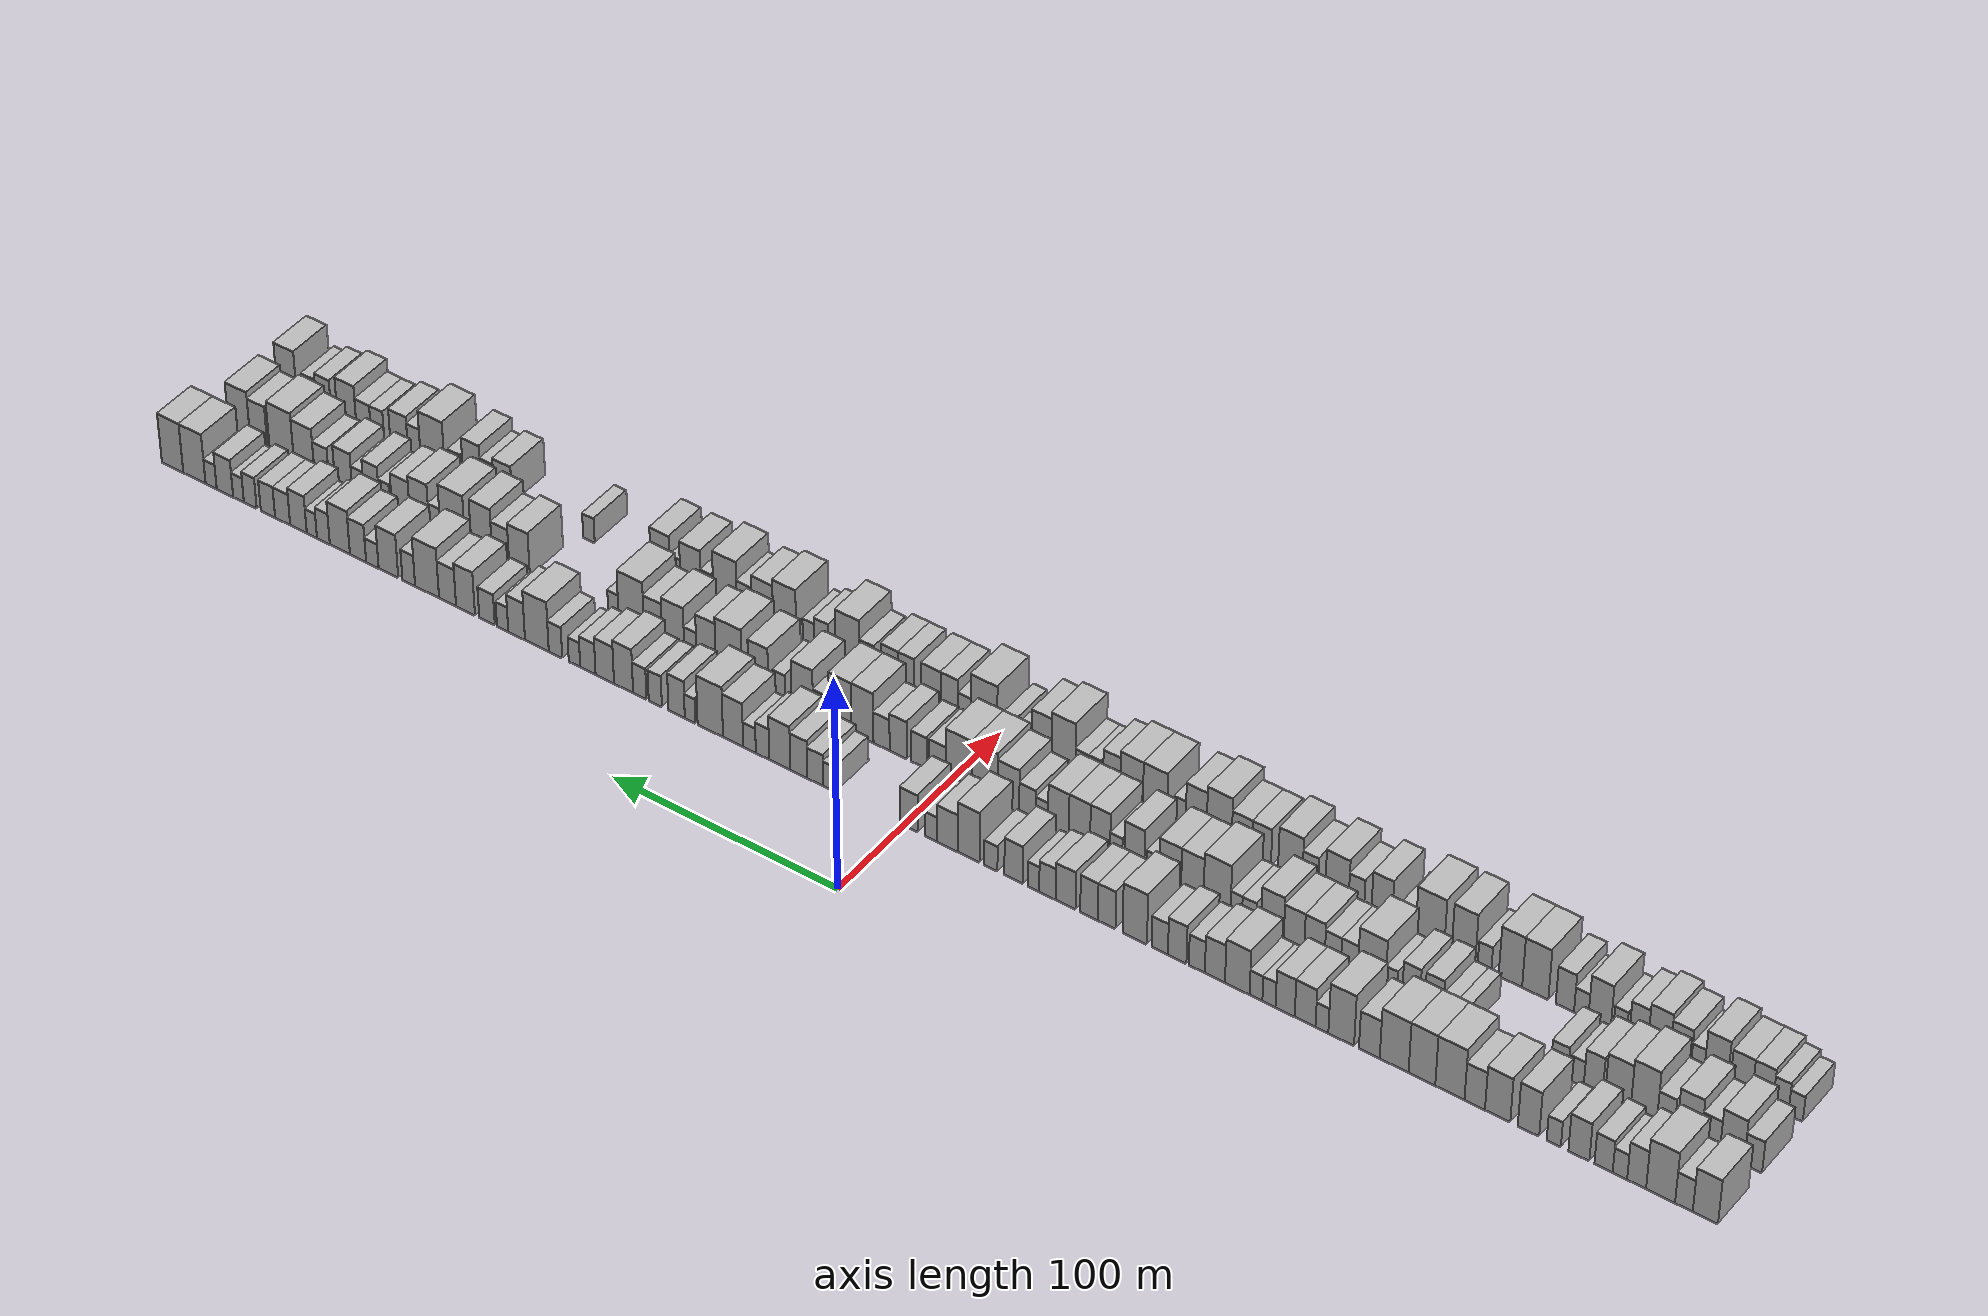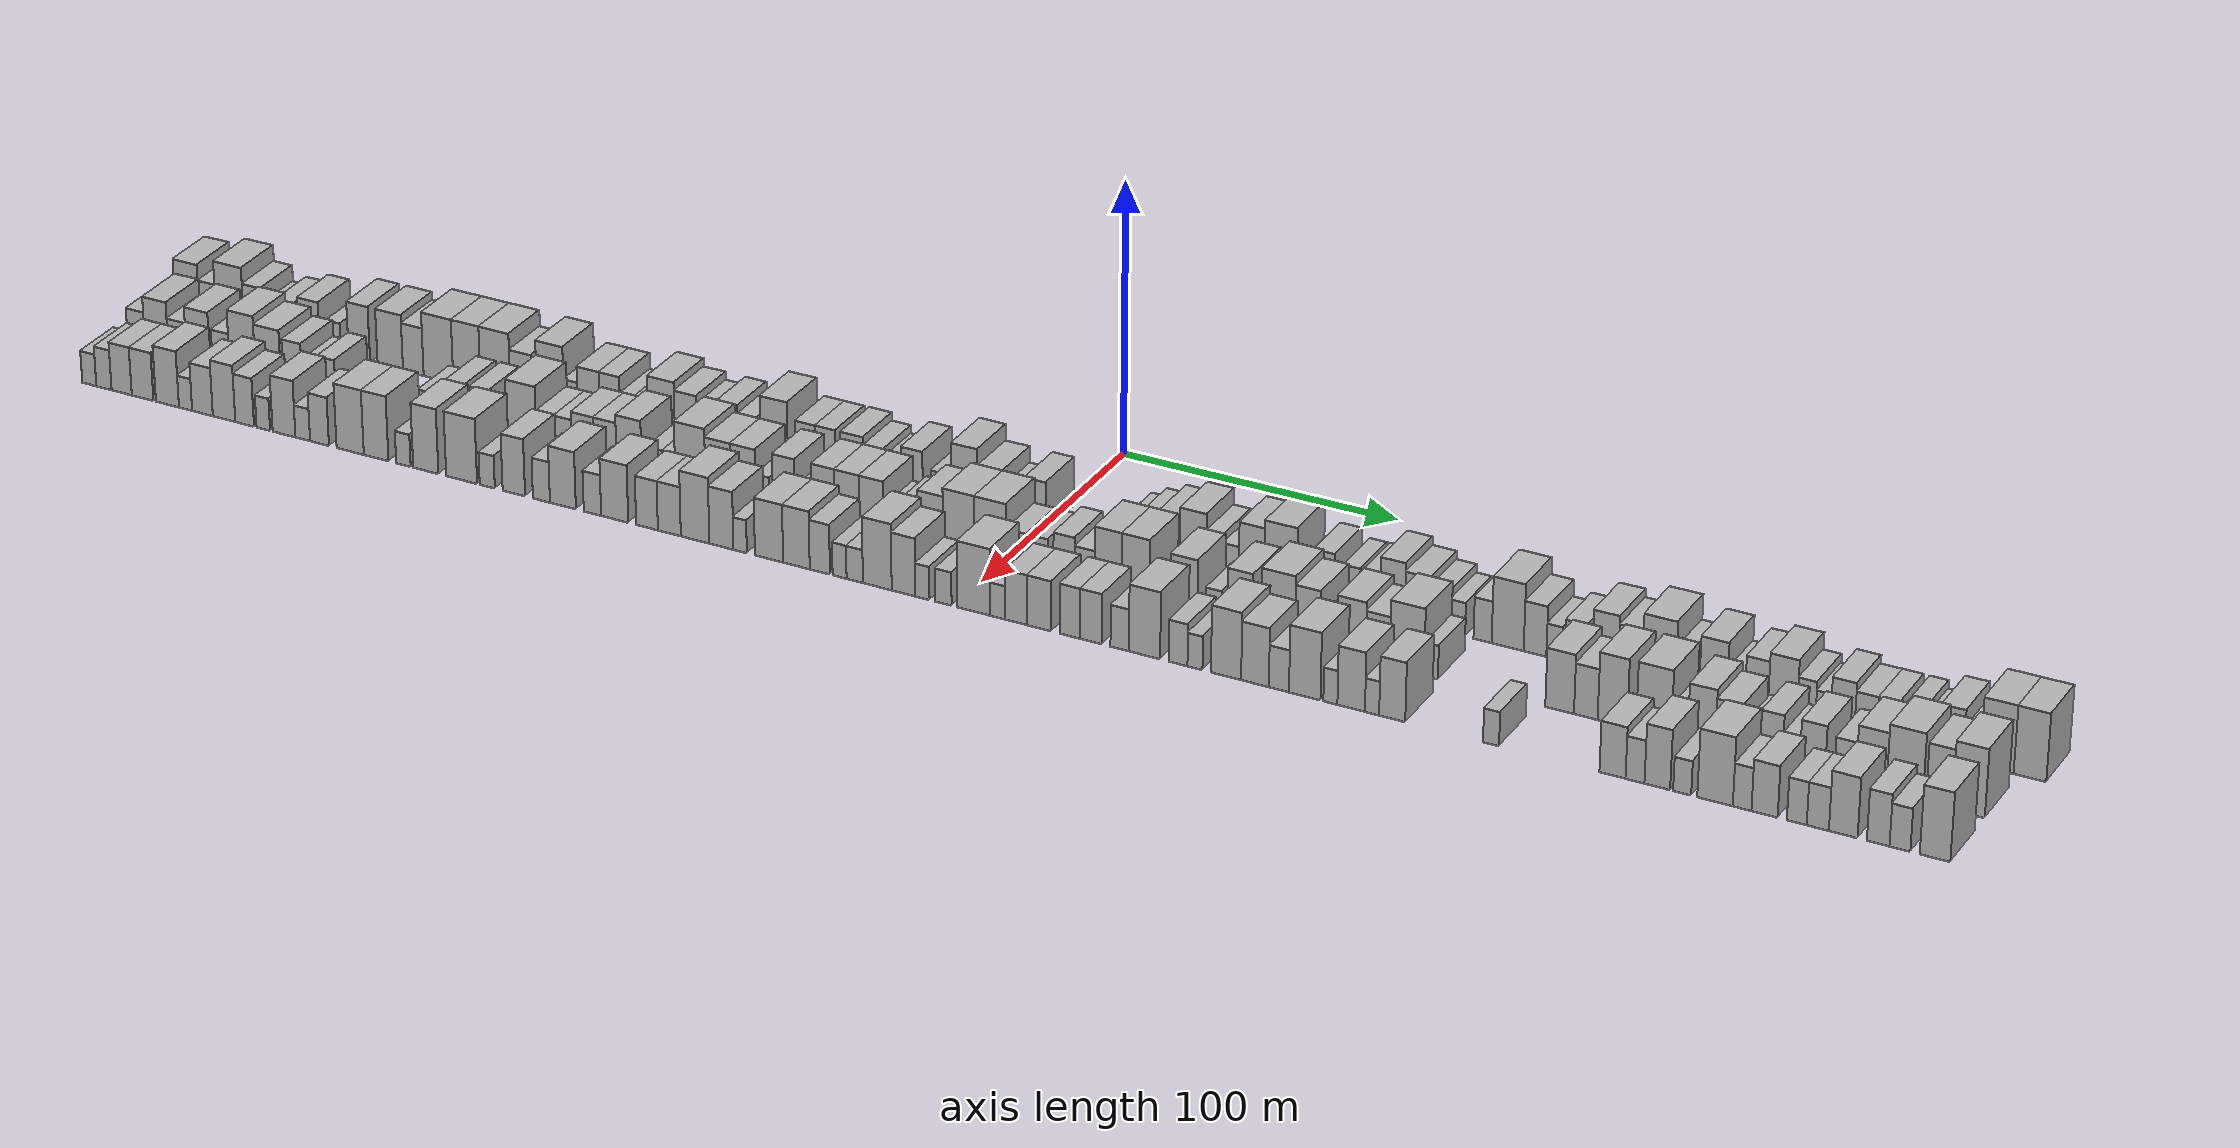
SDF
<sdf version="1.6">
 <world name="default">
  <scene>
   <sky><clouds><speed>12</speed></clouds></sky>
   <ambient>0.4 0.4 0.4 1</ambient>
   <background>0.7 0.7 0.7 1</background>
   <shadows>1</shadows>
  </scene>
  <gravity>0 0 -9.8066</gravity>
  <magnetic_field>6e-06 2.3e-05 -4.2e-05</magnetic_field>
  <physics default="0" name="default_physics" type="ode">
   <ode>
    <solver>
     <type>quick</type>
     <iters>10</iters>
     <sor>1.0</sor>
     <use_dynamic_moi_rescaling>0</use_dynamic_moi_rescaling>
    </solver>
    <constraints>
     <cfm>0</cfm>
     <erp>0.2</erp>
     <contact_max_correcting_vel>100</contact_max_correcting_vel>
     <contact_surface_layer>0.001</contact_surface_layer>
    </constraints>
   </ode>
   <max_step_size>0.004</max_step_size>
   <real_time_factor>1</real_time_factor>
   <real_time_update_rate>250</real_time_update_rate>
  </physics>
  <light name="sun" type="directional">
   <pose>0 0 10 0 0 0</pose>
   <diffuse>0.8 0.8 0.8 1</diffuse>
   <specular>0.2 0.2 0.2 1</specular>
   <attenuation>
    <range>1000</range>
    <constant>0.9</constant>
    <linear>0.01</linear>
    <quadratic>0.001</quadratic>
   </attenuation>
   <direction>-0.5 0.1 -0.9</direction>
  </light>
  <model name="building_1">
   <static>1</static>
   <pose>50.0000 -331.0890 0 0.000000 0.000000 0.000000</pose>
   <link name="link">
    <pose>0 0 10.50 0 0 0</pose>
    <collision name="collision"><geometry><box><size>20.0000 9.8219 21.0000</size></box></geometry></collision>
    <visual name="visual">
     <cast_shadows>0</cast_shadows>
     <geometry><box><size>20.0000 9.8219 21.0000</size></box></geometry>
     <material>
      <script>
       <uri>model://HANNAS_wall/materials/scripts</uri>
       <uri>model://HANNAS_wall/materials/textures</uri>
       <name>vrc/HANNAS_wall</name>
      </script>
     </material>
    </visual>
   </link>
  </model>
  <model name="building_2">
   <static>1</static>
   <pose>50.0000 -322.7180 0 0.000000 0.000000 0.000000</pose>
   <link name="link">
    <pose>0 0 7.50 0 0 0</pose>
    <collision name="collision"><geometry><box><size>20.0000 6.9202 15.0000</size></box></geometry></collision>
    <visual name="visual">
     <cast_shadows>0</cast_shadows>
     <geometry><box><size>20.0000 6.9202 15.0000</size></box></geometry>
     <material>
      <script>
       <uri>model://HANNAS_wall/materials/scripts</uri>
       <uri>model://HANNAS_wall/materials/textures</uri>
       <name>vrc/HANNAS_wall</name>
      </script>
     </material>
    </visual>
   </link>
  </model>
  <model name="building_3">
   <static>1</static>
   <pose>50.0000 -313.5908 0 0.000000 0.000000 0.000000</pose>
   <link name="link">
    <pose>0 0 12.00 0 0 0</pose>
    <collision name="collision"><geometry><box><size>20.0000 11.3343 24.0000</size></box></geometry></collision>
    <visual name="visual">
     <cast_shadows>0</cast_shadows>
     <geometry><box><size>20.0000 11.3343 24.0000</size></box></geometry>
     <material>
      <script>
       <uri>model://HANNAS_wall/materials/scripts</uri>
       <uri>model://HANNAS_wall/materials/textures</uri>
       <name>vrc/HANNAS_wall</name>
      </script>
     </material>
    </visual>
   </link>
  </model>
  <model name="building_4">
   <static>1</static>
   <pose>50.0000 -304.1958 0 0.000000 0.000000 0.000000</pose>
   <link name="link">
    <pose>0 0 9.00 0 0 0</pose>
    <collision name="collision"><geometry><box><size>20.0000 7.4557 18.0000</size></box></geometry></collision>
    <visual name="visual">
     <cast_shadows>0</cast_shadows>
     <geometry><box><size>20.0000 7.4557 18.0000</size></box></geometry>
     <material>
      <script>
       <uri>model://HANNAS_wall/materials/scripts</uri>
       <uri>model://HANNAS_wall/materials/textures</uri>
       <name>vrc/HANNAS_wall</name>
      </script>
     </material>
    </visual>
   </link>
  </model>
  <model name="building_5">
   <static>1</static>
   <pose>50.0000 -297.6287 0 0.000000 0.000000 0.000000</pose>
   <link name="link">
    <pose>0 0 6.00 0 0 0</pose>
    <collision name="collision"><geometry><box><size>20.0000 5.6784 12.0000</size></box></geometry></collision>
    <visual name="visual">
     <cast_shadows>0</cast_shadows>
     <geometry><box><size>20.0000 5.6784 12.0000</size></box></geometry>
     <material>
      <script>
       <uri>model://HANNAS_wall/materials/scripts</uri>
       <uri>model://HANNAS_wall/materials/textures</uri>
       <name>vrc/HANNAS_wall</name>
      </script>
     </material>
    </visual>
   </link>
  </model>
  <model name="building_6">
   <static>1</static>
   <pose>50.0000 -291.1822 0 0.000000 0.000000 0.000000</pose>
   <link name="link">
    <pose>0 0 7.50 0 0 0</pose>
    <collision name="collision"><geometry><box><size>20.0000 7.2147 15.0000</size></box></geometry></collision>
    <visual name="visual">
     <cast_shadows>0</cast_shadows>
     <geometry><box><size>20.0000 7.2147 15.0000</size></box></geometry>
     <material>
      <script>
       <uri>model://HANNAS_wall/materials/scripts</uri>
       <uri>model://HANNAS_wall/materials/textures</uri>
       <name>vrc/HANNAS_wall</name>
      </script>
     </material>
    </visual>
   </link>
  </model>
  <model name="building_7">
   <static>1</static>
   <pose>50.0000 -281.4151 0 0.000000 0.000000 0.000000</pose>
   <link name="link">
    <pose>0 0 9.00 0 0 0</pose>
    <collision name="collision"><geometry><box><size>20.0000 8.3195 18.0000</size></box></geometry></collision>
    <visual name="visual">
     <cast_shadows>0</cast_shadows>
     <geometry><box><size>20.0000 8.3195 18.0000</size></box></geometry>
     <material>
      <script>
       <uri>model://HANNAS_wall/materials/scripts</uri>
       <uri>model://HANNAS_wall/materials/textures</uri>
       <name>vrc/HANNAS_wall</name>
      </script>
     </material>
    </visual>
   </link>
  </model>
  <model name="building_8">
   <static>1</static>
   <pose>50.0000 -271.4453 0 0.000000 0.000000 0.000000</pose>
   <link name="link">
    <pose>0 0 6.00 0 0 0</pose>
    <collision name="collision"><geometry><box><size>20.0000 5.6200 12.0000</size></box></geometry></collision>
    <visual name="visual">
     <cast_shadows>0</cast_shadows>
     <geometry><box><size>20.0000 5.6200 12.0000</size></box></geometry>
     <material>
      <script>
       <uri>model://HANNAS_wall/materials/scripts</uri>
       <uri>model://HANNAS_wall/materials/textures</uri>
       <name>vrc/HANNAS_wall</name>
      </script>
     </material>
    </visual>
   </link>
  </model>
  <model name="building_9">
   <static>1</static>
   <pose>50.0000 -261.3609 0 0.000000 0.000000 0.000000</pose>
   <link name="link">
    <pose>0 0 10.50 0 0 0</pose>
    <collision name="collision"><geometry><box><size>20.0000 8.5488 21.0000</size></box></geometry></collision>
    <visual name="visual">
     <cast_shadows>0</cast_shadows>
     <geometry><box><size>20.0000 8.5488 21.0000</size></box></geometry>
     <material>
      <script>
       <uri>model://HANNAS_wall/materials/scripts</uri>
       <uri>model://HANNAS_wall/materials/textures</uri>
       <name>vrc/HANNAS_wall</name>
      </script>
     </material>
    </visual>
   </link>
  </model>
  <model name="building_10">
   <static>1</static>
   <pose>50.0000 -249.0100 0 0.000000 0.000000 0.000000</pose>
   <link name="link">
    <pose>0 0 10.50 0 0 0</pose>
    <collision name="collision"><geometry><box><size>20.0000 10.1530 21.0000</size></box></geometry></collision>
    <visual name="visual">
     <cast_shadows>0</cast_shadows>
     <geometry><box><size>20.0000 10.1530 21.0000</size></box></geometry>
     <material>
      <script>
       <uri>model://HANNAS_wall/materials/scripts</uri>
       <uri>model://HANNAS_wall/materials/textures</uri>
       <name>vrc/HANNAS_wall</name>
      </script>
     </material>
    </visual>
   </link>
  </model>
  <model name="building_11">
   <static>1</static>
   <pose>50.0000 -239.8170 0 0.000000 0.000000 0.000000</pose>
   <link name="link">
    <pose>0 0 9.00 0 0 0</pose>
    <collision name="collision"><geometry><box><size>20.0000 8.2330 18.0000</size></box></geometry></collision>
    <visual name="visual">
     <cast_shadows>0</cast_shadows>
     <geometry><box><size>20.0000 8.2330 18.0000</size></box></geometry>
     <material>
      <script>
       <uri>model://HANNAS_wall/materials/scripts</uri>
       <uri>model://HANNAS_wall/materials/textures</uri>
       <name>vrc/HANNAS_wall</name>
      </script>
     </material>
    </visual>
   </link>
  </model>
  <model name="building_12">
   <static>1</static>
   <pose>50.0000 -229.7973 0 0.000000 0.000000 0.000000</pose>
   <link name="link">
    <pose>0 0 12.00 0 0 0</pose>
    <collision name="collision"><geometry><box><size>20.0000 11.8064 24.0000</size></box></geometry></collision>
    <visual name="visual">
     <cast_shadows>0</cast_shadows>
     <geometry><box><size>20.0000 11.8064 24.0000</size></box></geometry>
     <material>
      <script>
       <uri>model://HANNAS_wall/materials/scripts</uri>
       <uri>model://HANNAS_wall/materials/textures</uri>
       <name>vrc/HANNAS_wall</name>
      </script>
     </material>
    </visual>
   </link>
  </model>
  <model name="building_13">
   <static>1</static>
   <pose>50.0000 -218.4713 0 0.000000 0.000000 0.000000</pose>
   <link name="link">
    <pose>0 0 12.00 0 0 0</pose>
    <collision name="collision"><geometry><box><size>20.0000 10.8456 24.0000</size></box></geometry></collision>
    <visual name="visual">
     <cast_shadows>0</cast_shadows>
     <geometry><box><size>20.0000 10.8456 24.0000</size></box></geometry>
     <material>
      <script>
       <uri>model://HANNAS_wall/materials/scripts</uri>
       <uri>model://HANNAS_wall/materials/textures</uri>
       <name>vrc/HANNAS_wall</name>
      </script>
     </material>
    </visual>
   </link>
  </model>
  <model name="building_14">
   <static>1</static>
   <pose>50.0000 -207.1681 0 0.000000 0.000000 0.000000</pose>
   <link name="link">
    <pose>0 0 12.00 0 0 0</pose>
    <collision name="collision"><geometry><box><size>20.0000 11.7610 24.0000</size></box></geometry></collision>
    <visual name="visual">
     <cast_shadows>0</cast_shadows>
     <geometry><box><size>20.0000 11.7610 24.0000</size></box></geometry>
     <material>
      <script>
       <uri>model://HANNAS_wall/materials/scripts</uri>
       <uri>model://HANNAS_wall/materials/textures</uri>
       <name>vrc/HANNAS_wall</name>
      </script>
     </material>
    </visual>
   </link>
  </model>
  <model name="building_15">
   <static>1</static>
   <pose>50.0000 -197.0413 0 0.000000 0.000000 0.000000</pose>
   <link name="link">
    <pose>0 0 9.00 0 0 0</pose>
    <collision name="collision"><geometry><box><size>20.0000 8.4925 18.0000</size></box></geometry></collision>
    <visual name="visual">
     <cast_shadows>0</cast_shadows>
     <geometry><box><size>20.0000 8.4925 18.0000</size></box></geometry>
     <material>
      <script>
       <uri>model://HANNAS_wall/materials/scripts</uri>
       <uri>model://HANNAS_wall/materials/textures</uri>
       <name>vrc/HANNAS_wall</name>
      </script>
     </material>
    </visual>
   </link>
  </model>
  <model name="building_16">
   <static>1</static>
   <pose>50.0000 -185.5123 0 0.000000 0.000000 0.000000</pose>
   <link name="link">
    <pose>0 0 12.00 0 0 0</pose>
    <collision name="collision"><geometry><box><size>20.0000 10.5657 24.0000</size></box></geometry></collision>
    <visual name="visual">
     <cast_shadows>0</cast_shadows>
     <geometry><box><size>20.0000 10.5657 24.0000</size></box></geometry>
     <material>
      <script>
       <uri>model://HANNAS_wall/materials/scripts</uri>
       <uri>model://HANNAS_wall/materials/textures</uri>
       <name>vrc/HANNAS_wall</name>
      </script>
     </material>
    </visual>
   </link>
  </model>
  <model name="building_17">
   <static>1</static>
   <pose>50.0000 -177.5832 0 0.000000 0.000000 0.000000</pose>
   <link name="link">
    <pose>0 0 6.00 0 0 0</pose>
    <collision name="collision"><geometry><box><size>20.0000 5.2924 12.0000</size></box></geometry></collision>
    <visual name="visual">
     <cast_shadows>0</cast_shadows>
     <geometry><box><size>20.0000 5.2924 12.0000</size></box></geometry>
     <material>
      <script>
       <uri>model://HANNAS_wall/materials/scripts</uri>
       <uri>model://HANNAS_wall/materials/textures</uri>
       <name>vrc/HANNAS_wall</name>
      </script>
     </material>
    </visual>
   </link>
  </model>
  <model name="building_18">
   <static>1</static>
   <pose>50.0000 -170.6352 0 0.000000 0.000000 0.000000</pose>
   <link name="link">
    <pose>0 0 9.00 0 0 0</pose>
    <collision name="collision"><geometry><box><size>20.0000 8.6036 18.0000</size></box></geometry></collision>
    <visual name="visual">
     <cast_shadows>0</cast_shadows>
     <geometry><box><size>20.0000 8.6036 18.0000</size></box></geometry>
     <material>
      <script>
       <uri>model://HANNAS_wall/materials/scripts</uri>
       <uri>model://HANNAS_wall/materials/textures</uri>
       <name>vrc/HANNAS_wall</name>
      </script>
     </material>
    </visual>
   </link>
  </model>
  <model name="building_19">
   <static>1</static>
   <pose>50.0000 -162.3650 0 0.000000 0.000000 0.000000</pose>
   <link name="link">
    <pose>0 0 9.00 0 0 0</pose>
    <collision name="collision"><geometry><box><size>20.0000 7.9368 18.0000</size></box></geometry></collision>
    <visual name="visual">
     <cast_shadows>0</cast_shadows>
     <geometry><box><size>20.0000 7.9368 18.0000</size></box></geometry>
     <material>
      <script>
       <uri>model://HANNAS_wall/materials/scripts</uri>
       <uri>model://HANNAS_wall/materials/textures</uri>
       <name>vrc/HANNAS_wall</name>
      </script>
     </material>
    </visual>
   </link>
  </model>
  <model name="building_20">
   <static>1</static>
   <pose>50.0000 -155.6761 0 0.000000 0.000000 0.000000</pose>
   <link name="link">
    <pose>0 0 6.00 0 0 0</pose>
    <collision name="collision"><geometry><box><size>20.0000 5.4409 12.0000</size></box></geometry></collision>
    <visual name="visual">
     <cast_shadows>0</cast_shadows>
     <geometry><box><size>20.0000 5.4409 12.0000</size></box></geometry>
     <material>
      <script>
       <uri>model://HANNAS_wall/materials/scripts</uri>
       <uri>model://HANNAS_wall/materials/textures</uri>
       <name>vrc/HANNAS_wall</name>
      </script>
     </material>
    </visual>
   </link>
  </model>
  <model name="building_21">
   <static>1</static>
   <pose>50.0000 -150.2887 0 0.000000 0.000000 0.000000</pose>
   <link name="link">
    <pose>0 0 6.00 0 0 0</pose>
    <collision name="collision"><geometry><box><size>20.0000 5.3338 12.0000</size></box></geometry></collision>
    <visual name="visual">
     <cast_shadows>0</cast_shadows>
     <geometry><box><size>20.0000 5.3338 12.0000</size></box></geometry>
     <material>
      <script>
       <uri>model://HANNAS_wall/materials/scripts</uri>
       <uri>model://HANNAS_wall/materials/textures</uri>
       <name>vrc/HANNAS_wall</name>
      </script>
     </material>
    </visual>
   </link>
  </model>
  <model name="building_22">
   <static>1</static>
   <pose>50.0000 -142.4901 0 0.000000 0.000000 0.000000</pose>
   <link name="link">
    <pose>0 0 10.50 0 0 0</pose>
    <collision name="collision"><geometry><box><size>20.0000 10.2634 21.0000</size></box></geometry></collision>
    <visual name="visual">
     <cast_shadows>0</cast_shadows>
     <geometry><box><size>20.0000 10.2634 21.0000</size></box></geometry>
     <material>
      <script>
       <uri>model://HANNAS_wall/materials/scripts</uri>
       <uri>model://HANNAS_wall/materials/textures</uri>
       <name>vrc/HANNAS_wall</name>
      </script>
     </material>
    </visual>
   </link>
  </model>
  <model name="building_23">
   <static>1</static>
   <pose>50.0000 -133.1389 0 0.000000 0.000000 0.000000</pose>
   <link name="link">
    <pose>0 0 9.00 0 0 0</pose>
    <collision name="collision"><geometry><box><size>20.0000 8.4390 18.0000</size></box></geometry></collision>
    <visual name="visual">
     <cast_shadows>0</cast_shadows>
     <geometry><box><size>20.0000 8.4390 18.0000</size></box></geometry>
     <material>
      <script>
       <uri>model://HANNAS_wall/materials/scripts</uri>
       <uri>model://HANNAS_wall/materials/textures</uri>
       <name>vrc/HANNAS_wall</name>
      </script>
     </material>
    </visual>
   </link>
  </model>
  <model name="building_24">
   <static>1</static>
   <pose>50.0000 -125.5603 0 0.000000 0.000000 0.000000</pose>
   <link name="link">
    <pose>0 0 7.50 0 0 0</pose>
    <collision name="collision"><geometry><box><size>20.0000 6.7183 15.0000</size></box></geometry></collision>
    <visual name="visual">
     <cast_shadows>0</cast_shadows>
     <geometry><box><size>20.0000 6.7183 15.0000</size></box></geometry>
     <material>
      <script>
       <uri>model://HANNAS_wall/materials/scripts</uri>
       <uri>model://HANNAS_wall/materials/textures</uri>
       <name>vrc/HANNAS_wall</name>
      </script>
     </material>
    </visual>
   </link>
  </model>
  <model name="building_25">
   <static>1</static>
   <pose>50.0000 -117.3013 0 0.000000 0.000000 0.000000</pose>
   <link name="link">
    <pose>0 0 9.00 0 0 0</pose>
    <collision name="collision"><geometry><box><size>20.0000 7.7996 18.0000</size></box></geometry></collision>
    <visual name="visual">
     <cast_shadows>0</cast_shadows>
     <geometry><box><size>20.0000 7.7996 18.0000</size></box></geometry>
     <material>
      <script>
       <uri>model://HANNAS_wall/materials/scripts</uri>
       <uri>model://HANNAS_wall/materials/textures</uri>
       <name>vrc/HANNAS_wall</name>
      </script>
     </material>
    </visual>
   </link>
  </model>
  <model name="building_26">
   <static>1</static>
   <pose>50.0000 -109.9660 0 0.000000 0.000000 0.000000</pose>
   <link name="link">
    <pose>0 0 7.50 0 0 0</pose>
    <collision name="collision"><geometry><box><size>20.0000 6.8709 15.0000</size></box></geometry></collision>
    <visual name="visual">
     <cast_shadows>0</cast_shadows>
     <geometry><box><size>20.0000 6.8709 15.0000</size></box></geometry>
     <material>
      <script>
       <uri>model://HANNAS_wall/materials/scripts</uri>
       <uri>model://HANNAS_wall/materials/textures</uri>
       <name>vrc/HANNAS_wall</name>
      </script>
     </material>
    </visual>
   </link>
  </model>
  <model name="building_27">
   <static>1</static>
   <pose>50.0000 -99.3671 0 0.000000 0.000000 0.000000</pose>
   <link name="link">
    <pose>0 0 12.00 0 0 0</pose>
    <collision name="collision"><geometry><box><size>20.0000 10.3270 24.0000</size></box></geometry></collision>
    <visual name="visual">
     <cast_shadows>0</cast_shadows>
     <geometry><box><size>20.0000 10.3270 24.0000</size></box></geometry>
     <material>
      <script>
       <uri>model://HANNAS_wall/materials/scripts</uri>
       <uri>model://HANNAS_wall/materials/textures</uri>
       <name>vrc/HANNAS_wall</name>
      </script>
     </material>
    </visual>
   </link>
  </model>
  <model name="building_28">
   <static>1</static>
   <pose>50.0000 -87.4475 0 0.000000 0.000000 0.000000</pose>
   <link name="link">
    <pose>0 0 9.00 0 0 0</pose>
    <collision name="collision"><geometry><box><size>20.0000 7.5122 18.0000</size></box></geometry></collision>
    <visual name="visual">
     <cast_shadows>0</cast_shadows>
     <geometry><box><size>20.0000 7.5122 18.0000</size></box></geometry>
     <material>
      <script>
       <uri>model://HANNAS_wall/materials/scripts</uri>
       <uri>model://HANNAS_wall/materials/textures</uri>
       <name>vrc/HANNAS_wall</name>
      </script>
     </material>
    </visual>
   </link>
  </model>
  <model name="building_29">
   <static>1</static>
   <pose>50.0000 -79.9290 0 0.000000 0.000000 0.000000</pose>
   <link name="link">
    <pose>0 0 9.00 0 0 0</pose>
    <collision name="collision"><geometry><box><size>20.0000 7.5247 18.0000</size></box></geometry></collision>
    <visual name="visual">
     <cast_shadows>0</cast_shadows>
     <geometry><box><size>20.0000 7.5247 18.0000</size></box></geometry>
     <material>
      <script>
       <uri>model://HANNAS_wall/materials/scripts</uri>
       <uri>model://HANNAS_wall/materials/textures</uri>
       <name>vrc/HANNAS_wall</name>
      </script>
     </material>
    </visual>
   </link>
  </model>
  <model name="building_30">
   <static>1</static>
   <pose>50.0000 -69.9789 0 0.000000 0.000000 0.000000</pose>
   <link name="link">
    <pose>0 0 9.00 0 0 0</pose>
    <collision name="collision"><geometry><box><size>20.0000 8.3756 18.0000</size></box></geometry></collision>
    <visual name="visual">
     <cast_shadows>0</cast_shadows>
     <geometry><box><size>20.0000 8.3756 18.0000</size></box></geometry>
     <material>
      <script>
       <uri>model://HANNAS_wall/materials/scripts</uri>
       <uri>model://HANNAS_wall/materials/textures</uri>
       <name>vrc/HANNAS_wall</name>
      </script>
     </material>
    </visual>
   </link>
  </model>
  <model name="building_31">
   <static>1</static>
   <pose>50.0000 -62.2029 0 0.000000 0.000000 0.000000</pose>
   <link name="link">
    <pose>0 0 7.50 0 0 0</pose>
    <collision name="collision"><geometry><box><size>20.0000 7.1765 15.0000</size></box></geometry></collision>
    <visual name="visual">
     <cast_shadows>0</cast_shadows>
     <geometry><box><size>20.0000 7.1765 15.0000</size></box></geometry>
     <material>
      <script>
       <uri>model://HANNAS_wall/materials/scripts</uri>
       <uri>model://HANNAS_wall/materials/textures</uri>
       <name>vrc/HANNAS_wall</name>
      </script>
     </material>
    </visual>
   </link>
  </model>
  <model name="building_32">
   <static>1</static>
   <pose>50.0000 -56.1010 0 0.000000 0.000000 0.000000</pose>
   <link name="link">
    <pose>0 0 6.00 0 0 0</pose>
    <collision name="collision"><geometry><box><size>20.0000 5.0273 12.0000</size></box></geometry></collision>
    <visual name="visual">
     <cast_shadows>0</cast_shadows>
     <geometry><box><size>20.0000 5.0273 12.0000</size></box></geometry>
     <material>
      <script>
       <uri>model://HANNAS_wall/materials/scripts</uri>
       <uri>model://HANNAS_wall/materials/textures</uri>
       <name>vrc/HANNAS_wall</name>
      </script>
     </material>
    </visual>
   </link>
  </model>
  <model name="building_33">
   <static>1</static>
   <pose>50.0000 -47.5748 0 0.000000 0.000000 0.000000</pose>
   <link name="link">
    <pose>0 0 9.00 0 0 0</pose>
    <collision name="collision"><geometry><box><size>20.0000 8.0251 18.0000</size></box></geometry></collision>
    <visual name="visual">
     <cast_shadows>0</cast_shadows>
     <geometry><box><size>20.0000 8.0251 18.0000</size></box></geometry>
     <material>
      <script>
       <uri>model://HANNAS_wall/materials/scripts</uri>
       <uri>model://HANNAS_wall/materials/textures</uri>
       <name>vrc/HANNAS_wall</name>
      </script>
     </material>
    </visual>
   </link>
  </model>
  <model name="building_34">
   <static>1</static>
   <pose>50.0000 -37.7320 0 0.000000 0.000000 0.000000</pose>
   <link name="link">
    <pose>0 0 6.00 0 0 0</pose>
    <collision name="collision"><geometry><box><size>20.0000 5.6603 12.0000</size></box></geometry></collision>
    <visual name="visual">
     <cast_shadows>0</cast_shadows>
     <geometry><box><size>20.0000 5.6603 12.0000</size></box></geometry>
     <material>
      <script>
       <uri>model://HANNAS_wall/materials/scripts</uri>
       <uri>model://HANNAS_wall/materials/textures</uri>
       <name>vrc/HANNAS_wall</name>
      </script>
     </material>
    </visual>
   </link>
  </model>
  <model name="building_35">
   <static>1</static>
   <pose>50.0000 -28.0791 0 0.000000 0.000000 0.000000</pose>
   <link name="link">
    <pose>0 0 12.00 0 0 0</pose>
    <collision name="collision"><geometry><box><size>20.0000 9.6455 24.0000</size></box></geometry></collision>
    <visual name="visual">
     <cast_shadows>0</cast_shadows>
     <geometry><box><size>20.0000 9.6455 24.0000</size></box></geometry>
     <material>
      <script>
       <uri>model://HANNAS_wall/materials/scripts</uri>
       <uri>model://HANNAS_wall/materials/textures</uri>
       <name>vrc/HANNAS_wall</name>
      </script>
     </material>
    </visual>
   </link>
  </model>
  <model name="building_36">
   <static>1</static>
   <pose>50.0000 -18.7964 0 0.000000 0.000000 0.000000</pose>
   <link name="link">
    <pose>0 0 9.00 0 0 0</pose>
    <collision name="collision"><geometry><box><size>20.0000 8.9199 18.0000</size></box></geometry></collision>
    <visual name="visual">
     <cast_shadows>0</cast_shadows>
     <geometry><box><size>20.0000 8.9199 18.0000</size></box></geometry>
     <material>
      <script>
       <uri>model://HANNAS_wall/materials/scripts</uri>
       <uri>model://HANNAS_wall/materials/textures</uri>
       <name>vrc/HANNAS_wall</name>
      </script>
     </material>
    </visual>
   </link>
  </model>
  <model name="building_37">
   <static>1</static>
   <pose>50.0000 -11.6247 0 0.000000 0.000000 0.000000</pose>
   <link name="link">
    <pose>0 0 6.00 0 0 0</pose>
    <collision name="collision"><geometry><box><size>20.0000 5.4235 12.0000</size></box></geometry></collision>
    <visual name="visual">
     <cast_shadows>0</cast_shadows>
     <geometry><box><size>20.0000 5.4235 12.0000</size></box></geometry>
     <material>
      <script>
       <uri>model://HANNAS_wall/materials/scripts</uri>
       <uri>model://HANNAS_wall/materials/textures</uri>
       <name>vrc/HANNAS_wall</name>
      </script>
     </material>
    </visual>
   </link>
  </model>
  <model name="building_38">
   <static>1</static>
   <pose>50.0000 -2.0124 0 0.000000 0.000000 0.000000</pose>
   <link name="link">
    <pose>0 0 9.00 0 0 0</pose>
    <collision name="collision"><geometry><box><size>20.0000 7.8012 18.0000</size></box></geometry></collision>
    <visual name="visual">
     <cast_shadows>0</cast_shadows>
     <geometry><box><size>20.0000 7.8012 18.0000</size></box></geometry>
     <material>
      <script>
       <uri>model://HANNAS_wall/materials/scripts</uri>
       <uri>model://HANNAS_wall/materials/textures</uri>
       <name>vrc/HANNAS_wall</name>
      </script>
     </material>
    </visual>
   </link>
  </model>
  <model name="building_39">
   <static>1</static>
   <pose>50.0000 33.1125 0 0.000000 0.000000 0.000000</pose>
   <link name="link">
    <pose>0 0 6.00 0 0 0</pose>
    <collision name="collision"><geometry><box><size>20.0000 5.4829 12.0000</size></box></geometry></collision>
    <visual name="visual">
     <cast_shadows>0</cast_shadows>
     <geometry><box><size>20.0000 5.4829 12.0000</size></box></geometry>
     <material>
      <script>
       <uri>model://HANNAS_wall/materials/scripts</uri>
       <uri>model://HANNAS_wall/materials/textures</uri>
       <name>vrc/HANNAS_wall</name>
      </script>
     </material>
    </visual>
   </link>
  </model>
  <model name="building_40">
   <static>1</static>
   <pose>50.0000 39.4169 0 0.000000 0.000000 0.000000</pose>
   <link name="link">
    <pose>0 0 7.50 0 0 0</pose>
    <collision name="collision"><geometry><box><size>20.0000 7.1260 15.0000</size></box></geometry></collision>
    <visual name="visual">
     <cast_shadows>0</cast_shadows>
     <geometry><box><size>20.0000 7.1260 15.0000</size></box></geometry>
     <material>
      <script>
       <uri>model://HANNAS_wall/materials/scripts</uri>
       <uri>model://HANNAS_wall/materials/textures</uri>
       <name>vrc/HANNAS_wall</name>
      </script>
     </material>
    </visual>
   </link>
  </model>
  <model name="building_41">
   <static>1</static>
   <pose>50.0000 46.7882 0 0.000000 0.000000 0.000000</pose>
   <link name="link">
    <pose>0 0 9.00 0 0 0</pose>
    <collision name="collision"><geometry><box><size>20.0000 7.6165 18.0000</size></box></geometry></collision>
    <visual name="visual">
     <cast_shadows>0</cast_shadows>
     <geometry><box><size>20.0000 7.6165 18.0000</size></box></geometry>
     <material>
      <script>
       <uri>model://HANNAS_wall/materials/scripts</uri>
       <uri>model://HANNAS_wall/materials/textures</uri>
       <name>vrc/HANNAS_wall</name>
      </script>
     </material>
    </visual>
   </link>
  </model>
  <model name="building_42">
   <static>1</static>
   <pose>50.0000 55.3181 0 0.000000 0.000000 0.000000</pose>
   <link name="link">
    <pose>0 0 10.50 0 0 0</pose>
    <collision name="collision"><geometry><box><size>20.0000 9.4433 21.0000</size></box></geometry></collision>
    <visual name="visual">
     <cast_shadows>0</cast_shadows>
     <geometry><box><size>20.0000 9.4433 21.0000</size></box></geometry>
     <material>
      <script>
       <uri>model://HANNAS_wall/materials/scripts</uri>
       <uri>model://HANNAS_wall/materials/textures</uri>
       <name>vrc/HANNAS_wall</name>
      </script>
     </material>
    </visual>
   </link>
  </model>
  <model name="building_43">
   <static>1</static>
   <pose>50.0000 63.0514 0 0.000000 0.000000 0.000000</pose>
   <link name="link">
    <pose>0 0 7.50 0 0 0</pose>
    <collision name="collision"><geometry><box><size>20.0000 6.0235 15.0000</size></box></geometry></collision>
    <visual name="visual">
     <cast_shadows>0</cast_shadows>
     <geometry><box><size>20.0000 6.0235 15.0000</size></box></geometry>
     <material>
      <script>
       <uri>model://HANNAS_wall/materials/scripts</uri>
       <uri>model://HANNAS_wall/materials/textures</uri>
       <name>vrc/HANNAS_wall</name>
      </script>
     </material>
    </visual>
   </link>
  </model>
  <model name="building_44">
   <static>1</static>
   <pose>50.0000 68.9114 0 0.000000 0.000000 0.000000</pose>
   <link name="link">
    <pose>0 0 6.00 0 0 0</pose>
    <collision name="collision"><geometry><box><size>20.0000 5.6965 12.0000</size></box></geometry></collision>
    <visual name="visual">
     <cast_shadows>0</cast_shadows>
     <geometry><box><size>20.0000 5.6965 12.0000</size></box></geometry>
     <material>
      <script>
       <uri>model://HANNAS_wall/materials/scripts</uri>
       <uri>model://HANNAS_wall/materials/textures</uri>
       <name>vrc/HANNAS_wall</name>
      </script>
     </material>
    </visual>
   </link>
  </model>
  <model name="building_45">
   <static>1</static>
   <pose>50.0000 76.3164 0 0.000000 0.000000 0.000000</pose>
   <link name="link">
    <pose>0 0 10.50 0 0 0</pose>
    <collision name="collision"><geometry><box><size>20.0000 9.1134 21.0000</size></box></geometry></collision>
    <visual name="visual">
     <cast_shadows>0</cast_shadows>
     <geometry><box><size>20.0000 9.1134 21.0000</size></box></geometry>
     <material>
      <script>
       <uri>model://HANNAS_wall/materials/scripts</uri>
       <uri>model://HANNAS_wall/materials/textures</uri>
       <name>vrc/HANNAS_wall</name>
      </script>
     </material>
    </visual>
   </link>
  </model>
  <model name="building_46">
   <static>1</static>
   <pose>50.0000 86.6233 0 0.000000 0.000000 0.000000</pose>
   <link name="link">
    <pose>0 0 12.00 0 0 0</pose>
    <collision name="collision"><geometry><box><size>20.0000 11.5006 24.0000</size></box></geometry></collision>
    <visual name="visual">
     <cast_shadows>0</cast_shadows>
     <geometry><box><size>20.0000 11.5006 24.0000</size></box></geometry>
     <material>
      <script>
       <uri>model://HANNAS_wall/materials/scripts</uri>
       <uri>model://HANNAS_wall/materials/textures</uri>
       <name>vrc/HANNAS_wall</name>
      </script>
     </material>
    </visual>
   </link>
  </model>
  <model name="building_47">
   <static>1</static>
   <pose>50.0000 95.7858 0 0.000000 0.000000 0.000000</pose>
   <link name="link">
    <pose>0 0 6.00 0 0 0</pose>
    <collision name="collision"><geometry><box><size>20.0000 4.8242 12.0000</size></box></geometry></collision>
    <visual name="visual">
     <cast_shadows>0</cast_shadows>
     <geometry><box><size>20.0000 4.8242 12.0000</size></box></geometry>
     <material>
      <script>
       <uri>model://HANNAS_wall/materials/scripts</uri>
       <uri>model://HANNAS_wall/materials/textures</uri>
       <name>vrc/HANNAS_wall</name>
      </script>
     </material>
    </visual>
   </link>
  </model>
  <model name="building_48">
   <static>1</static>
   <pose>50.0000 101.9094 0 0.000000 0.000000 0.000000</pose>
   <link name="link">
    <pose>0 0 9.00 0 0 0</pose>
    <collision name="collision"><geometry><box><size>20.0000 7.4231 18.0000</size></box></geometry></collision>
    <visual name="visual">
     <cast_shadows>0</cast_shadows>
     <geometry><box><size>20.0000 7.4231 18.0000</size></box></geometry>
     <material>
      <script>
       <uri>model://HANNAS_wall/materials/scripts</uri>
       <uri>model://HANNAS_wall/materials/textures</uri>
       <name>vrc/HANNAS_wall</name>
      </script>
     </material>
    </visual>
   </link>
  </model>
  <model name="building_49">
   <static>1</static>
   <pose>50.0000 111.6408 0 0.000000 0.000000 0.000000</pose>
   <link name="link">
    <pose>0 0 7.50 0 0 0</pose>
    <collision name="collision"><geometry><box><size>20.0000 6.0397 15.0000</size></box></geometry></collision>
    <visual name="visual">
     <cast_shadows>0</cast_shadows>
     <geometry><box><size>20.0000 6.0397 15.0000</size></box></geometry>
     <material>
      <script>
       <uri>model://HANNAS_wall/materials/scripts</uri>
       <uri>model://HANNAS_wall/materials/textures</uri>
       <name>vrc/HANNAS_wall</name>
      </script>
     </material>
    </visual>
   </link>
  </model>
  <model name="building_50">
   <static>1</static>
   <pose>50.0000 118.7300 0 0.000000 0.000000 0.000000</pose>
   <link name="link">
    <pose>0 0 7.50 0 0 0</pose>
    <collision name="collision"><geometry><box><size>20.0000 6.1386 15.0000</size></box></geometry></collision>
    <visual name="visual">
     <cast_shadows>0</cast_shadows>
     <geometry><box><size>20.0000 6.1386 15.0000</size></box></geometry>
     <material>
      <script>
       <uri>model://HANNAS_wall/materials/scripts</uri>
       <uri>model://HANNAS_wall/materials/textures</uri>
       <name>vrc/HANNAS_wall</name>
      </script>
     </material>
    </visual>
   </link>
  </model>
  <model name="building_51">
   <static>1</static>
   <pose>50.0000 126.1779 0 0.000000 0.000000 0.000000</pose>
   <link name="link">
    <pose>0 0 10.50 0 0 0</pose>
    <collision name="collision"><geometry><box><size>20.0000 8.7572 21.0000</size></box></geometry></collision>
    <visual name="visual">
     <cast_shadows>0</cast_shadows>
     <geometry><box><size>20.0000 8.7572 21.0000</size></box></geometry>
     <material>
      <script>
       <uri>model://HANNAS_wall/materials/scripts</uri>
       <uri>model://HANNAS_wall/materials/textures</uri>
       <name>vrc/HANNAS_wall</name>
      </script>
     </material>
    </visual>
   </link>
  </model>
  <model name="building_52">
   <static>1</static>
   <pose>50.0000 134.8192 0 0.000000 0.000000 0.000000</pose>
   <link name="link">
    <pose>0 0 9.00 0 0 0</pose>
    <collision name="collision"><geometry><box><size>20.0000 8.5254 18.0000</size></box></geometry></collision>
    <visual name="visual">
     <cast_shadows>0</cast_shadows>
     <geometry><box><size>20.0000 8.5254 18.0000</size></box></geometry>
     <material>
      <script>
       <uri>model://HANNAS_wall/materials/scripts</uri>
       <uri>model://HANNAS_wall/materials/textures</uri>
       <name>vrc/HANNAS_wall</name>
      </script>
     </material>
    </visual>
   </link>
  </model>
  <model name="building_53">
   <static>1</static>
   <pose>50.0000 142.6200 0 0.000000 0.000000 0.000000</pose>
   <link name="link">
    <pose>0 0 7.50 0 0 0</pose>
    <collision name="collision"><geometry><box><size>20.0000 7.0762 15.0000</size></box></geometry></collision>
    <visual name="visual">
     <cast_shadows>0</cast_shadows>
     <geometry><box><size>20.0000 7.0762 15.0000</size></box></geometry>
     <material>
      <script>
       <uri>model://HANNAS_wall/materials/scripts</uri>
       <uri>model://HANNAS_wall/materials/textures</uri>
       <name>vrc/HANNAS_wall</name>
      </script>
     </material>
    </visual>
   </link>
  </model>
  <model name="building_54">
   <static>1</static>
   <pose>50.0000 148.8236 0 0.000000 0.000000 0.000000</pose>
   <link name="link">
    <pose>0 0 6.00 0 0 0</pose>
    <collision name="collision"><geometry><box><size>20.0000 5.3311 12.0000</size></box></geometry></collision>
    <visual name="visual">
     <cast_shadows>0</cast_shadows>
     <geometry><box><size>20.0000 5.3311 12.0000</size></box></geometry>
     <material>
      <script>
       <uri>model://HANNAS_wall/materials/scripts</uri>
       <uri>model://HANNAS_wall/materials/textures</uri>
       <name>vrc/HANNAS_wall</name>
      </script>
     </material>
    </visual>
   </link>
  </model>
  <model name="building_55">
   <static>1</static>
   <pose>50.0000 157.6245 0 0.000000 0.000000 0.000000</pose>
   <link name="link">
    <pose>0 0 7.50 0 0 0</pose>
    <collision name="collision"><geometry><box><size>20.0000 6.2707 15.0000</size></box></geometry></collision>
    <visual name="visual">
     <cast_shadows>0</cast_shadows>
     <geometry><box><size>20.0000 6.2707 15.0000</size></box></geometry>
     <material>
      <script>
       <uri>model://HANNAS_wall/materials/scripts</uri>
       <uri>model://HANNAS_wall/materials/textures</uri>
       <name>vrc/HANNAS_wall</name>
      </script>
     </material>
    </visual>
   </link>
  </model>
  <model name="building_56">
   <static>1</static>
   <pose>50.0000 166.3002 0 0.000000 0.000000 0.000000</pose>
   <link name="link">
    <pose>0 0 12.00 0 0 0</pose>
    <collision name="collision"><geometry><box><size>20.0000 11.0808 24.0000</size></box></geometry></collision>
    <visual name="visual">
     <cast_shadows>0</cast_shadows>
     <geometry><box><size>20.0000 11.0808 24.0000</size></box></geometry>
     <material>
      <script>
       <uri>model://HANNAS_wall/materials/scripts</uri>
       <uri>model://HANNAS_wall/materials/textures</uri>
       <name>vrc/HANNAS_wall</name>
      </script>
     </material>
    </visual>
   </link>
  </model>
  <model name="building_57">
   <static>1</static>
   <pose>50.0000 175.7462 0 0.000000 0.000000 0.000000</pose>
   <link name="link">
    <pose>0 0 9.00 0 0 0</pose>
    <collision name="collision"><geometry><box><size>20.0000 7.8112 18.0000</size></box></geometry></collision>
    <visual name="visual">
     <cast_shadows>0</cast_shadows>
     <geometry><box><size>20.0000 7.8112 18.0000</size></box></geometry>
     <material>
      <script>
       <uri>model://HANNAS_wall/materials/scripts</uri>
       <uri>model://HANNAS_wall/materials/textures</uri>
       <name>vrc/HANNAS_wall</name>
      </script>
     </material>
    </visual>
   </link>
  </model>
  <model name="building_58">
   <static>1</static>
   <pose>50.0000 182.2998 0 0.000000 0.000000 0.000000</pose>
   <link name="link">
    <pose>0 0 6.00 0 0 0</pose>
    <collision name="collision"><geometry><box><size>20.0000 5.2960 12.0000</size></box></geometry></collision>
    <visual name="visual">
     <cast_shadows>0</cast_shadows>
     <geometry><box><size>20.0000 5.2960 12.0000</size></box></geometry>
     <material>
      <script>
       <uri>model://HANNAS_wall/materials/scripts</uri>
       <uri>model://HANNAS_wall/materials/textures</uri>
       <name>vrc/HANNAS_wall</name>
      </script>
     </material>
    </visual>
   </link>
  </model>
  <model name="building_59">
   <static>1</static>
   <pose>50.0000 189.6086 0 0.000000 0.000000 0.000000</pose>
   <link name="link">
    <pose>0 0 7.50 0 0 0</pose>
    <collision name="collision"><geometry><box><size>20.0000 7.3216 15.0000</size></box></geometry></collision>
    <visual name="visual">
     <cast_shadows>0</cast_shadows>
     <geometry><box><size>20.0000 7.3216 15.0000</size></box></geometry>
     <material>
      <script>
       <uri>model://HANNAS_wall/materials/scripts</uri>
       <uri>model://HANNAS_wall/materials/textures</uri>
       <name>vrc/HANNAS_wall</name>
      </script>
     </material>
    </visual>
   </link>
  </model>
  <model name="building_60">
   <static>1</static>
   <pose>50.0000 199.7213 0 0.000000 0.000000 0.000000</pose>
   <link name="link">
    <pose>0 0 10.50 0 0 0</pose>
    <collision name="collision"><geometry><box><size>20.0000 8.9038 21.0000</size></box></geometry></collision>
    <visual name="visual">
     <cast_shadows>0</cast_shadows>
     <geometry><box><size>20.0000 8.9038 21.0000</size></box></geometry>
     <material>
      <script>
       <uri>model://HANNAS_wall/materials/scripts</uri>
       <uri>model://HANNAS_wall/materials/textures</uri>
       <name>vrc/HANNAS_wall</name>
      </script>
     </material>
    </visual>
   </link>
  </model>
  <model name="building_61">
   <static>1</static>
   <pose>50.0000 208.2026 0 0.000000 0.000000 0.000000</pose>
   <link name="link">
    <pose>0 0 9.00 0 0 0</pose>
    <collision name="collision"><geometry><box><size>20.0000 8.0587 18.0000</size></box></geometry></collision>
    <visual name="visual">
     <cast_shadows>0</cast_shadows>
     <geometry><box><size>20.0000 8.0587 18.0000</size></box></geometry>
     <material>
      <script>
       <uri>model://HANNAS_wall/materials/scripts</uri>
       <uri>model://HANNAS_wall/materials/textures</uri>
       <name>vrc/HANNAS_wall</name>
      </script>
     </material>
    </visual>
   </link>
  </model>
  <model name="building_62">
   <static>1</static>
   <pose>50.0000 217.9049 0 0.000000 0.000000 0.000000</pose>
   <link name="link">
    <pose>0 0 12.00 0 0 0</pose>
    <collision name="collision"><geometry><box><size>20.0000 11.3460 24.0000</size></box></geometry></collision>
    <visual name="visual">
     <cast_shadows>0</cast_shadows>
     <geometry><box><size>20.0000 11.3460 24.0000</size></box></geometry>
     <material>
      <script>
       <uri>model://HANNAS_wall/materials/scripts</uri>
       <uri>model://HANNAS_wall/materials/textures</uri>
       <name>vrc/HANNAS_wall</name>
      </script>
     </material>
    </visual>
   </link>
  </model>
  <model name="building_63">
   <static>1</static>
   <pose>50.0000 226.5868 0 0.000000 0.000000 0.000000</pose>
   <link name="link">
    <pose>0 0 7.50 0 0 0</pose>
    <collision name="collision"><geometry><box><size>20.0000 6.0177 15.0000</size></box></geometry></collision>
    <visual name="visual">
     <cast_shadows>0</cast_shadows>
     <geometry><box><size>20.0000 6.0177 15.0000</size></box></geometry>
     <material>
      <script>
       <uri>model://HANNAS_wall/materials/scripts</uri>
       <uri>model://HANNAS_wall/materials/textures</uri>
       <name>vrc/HANNAS_wall</name>
      </script>
     </material>
    </visual>
   </link>
  </model>
  <model name="building_64">
   <static>1</static>
   <pose>50.0000 236.2916 0 0.000000 0.000000 0.000000</pose>
   <link name="link">
    <pose>0 0 10.50 0 0 0</pose>
    <collision name="collision"><geometry><box><size>20.0000 9.3919 21.0000</size></box></geometry></collision>
    <visual name="visual">
     <cast_shadows>0</cast_shadows>
     <geometry><box><size>20.0000 9.3919 21.0000</size></box></geometry>
     <material>
      <script>
       <uri>model://HANNAS_wall/materials/scripts</uri>
       <uri>model://HANNAS_wall/materials/textures</uri>
       <name>vrc/HANNAS_wall</name>
      </script>
     </material>
    </visual>
   </link>
  </model>
  <model name="building_65">
   <static>1</static>
   <pose>50.0000 243.9687 0 0.000000 0.000000 0.000000</pose>
   <link name="link">
    <pose>0 0 6.00 0 0 0</pose>
    <collision name="collision"><geometry><box><size>20.0000 5.9624 12.0000</size></box></geometry></collision>
    <visual name="visual">
     <cast_shadows>0</cast_shadows>
     <geometry><box><size>20.0000 5.9624 12.0000</size></box></geometry>
     <material>
      <script>
       <uri>model://HANNAS_wall/materials/scripts</uri>
       <uri>model://HANNAS_wall/materials/textures</uri>
       <name>vrc/HANNAS_wall</name>
      </script>
     </material>
    </visual>
   </link>
  </model>
  <model name="building_66">
   <static>1</static>
   <pose>50.0000 250.8356 0 0.000000 0.000000 0.000000</pose>
   <link name="link">
    <pose>0 0 9.00 0 0 0</pose>
    <collision name="collision"><geometry><box><size>20.0000 7.7714 18.0000</size></box></geometry></collision>
    <visual name="visual">
     <cast_shadows>0</cast_shadows>
     <geometry><box><size>20.0000 7.7714 18.0000</size></box></geometry>
     <material>
      <script>
       <uri>model://HANNAS_wall/materials/scripts</uri>
       <uri>model://HANNAS_wall/materials/textures</uri>
       <name>vrc/HANNAS_wall</name>
      </script>
     </material>
    </visual>
   </link>
  </model>
  <model name="building_67">
   <static>1</static>
   <pose>50.0000 259.5712 0 0.000000 0.000000 0.000000</pose>
   <link name="link">
    <pose>0 0 10.50 0 0 0</pose>
    <collision name="collision"><geometry><box><size>20.0000 9.6997 21.0000</size></box></geometry></collision>
    <visual name="visual">
     <cast_shadows>0</cast_shadows>
     <geometry><box><size>20.0000 9.6997 21.0000</size></box></geometry>
     <material>
      <script>
       <uri>model://HANNAS_wall/materials/scripts</uri>
       <uri>model://HANNAS_wall/materials/textures</uri>
       <name>vrc/HANNAS_wall</name>
      </script>
     </material>
    </visual>
   </link>
  </model>
  <model name="building_68">
   <static>1</static>
   <pose>50.0000 267.5066 0 0.000000 0.000000 0.000000</pose>
   <link name="link">
    <pose>0 0 7.50 0 0 0</pose>
    <collision name="collision"><geometry><box><size>20.0000 6.1711 15.0000</size></box></geometry></collision>
    <visual name="visual">
     <cast_shadows>0</cast_shadows>
     <geometry><box><size>20.0000 6.1711 15.0000</size></box></geometry>
     <material>
      <script>
       <uri>model://HANNAS_wall/materials/scripts</uri>
       <uri>model://HANNAS_wall/materials/textures</uri>
       <name>vrc/HANNAS_wall</name>
      </script>
     </material>
    </visual>
   </link>
  </model>
  <model name="building_69">
   <static>1</static>
   <pose>50.0000 273.0611 0 0.000000 0.000000 0.000000</pose>
   <link name="link">
    <pose>0 0 6.00 0 0 0</pose>
    <collision name="collision"><geometry><box><size>20.0000 4.9380 12.0000</size></box></geometry></collision>
    <visual name="visual">
     <cast_shadows>0</cast_shadows>
     <geometry><box><size>20.0000 4.9380 12.0000</size></box></geometry>
     <material>
      <script>
       <uri>model://HANNAS_wall/materials/scripts</uri>
       <uri>model://HANNAS_wall/materials/textures</uri>
       <name>vrc/HANNAS_wall</name>
      </script>
     </material>
    </visual>
   </link>
  </model>
  <model name="building_70">
   <static>1</static>
   <pose>50.0000 279.5484 0 0.000000 0.000000 0.000000</pose>
   <link name="link">
    <pose>0 0 9.00 0 0 0</pose>
    <collision name="collision"><geometry><box><size>20.0000 8.0365 18.0000</size></box></geometry></collision>
    <visual name="visual">
     <cast_shadows>0</cast_shadows>
     <geometry><box><size>20.0000 8.0365 18.0000</size></box></geometry>
     <material>
      <script>
       <uri>model://HANNAS_wall/materials/scripts</uri>
       <uri>model://HANNAS_wall/materials/textures</uri>
       <name>vrc/HANNAS_wall</name>
      </script>
     </material>
    </visual>
   </link>
  </model>
  <model name="building_71">
   <static>1</static>
   <pose>50.0000 287.2281 0 0.000000 0.000000 0.000000</pose>
   <link name="link">
    <pose>0 0 7.50 0 0 0</pose>
    <collision name="collision"><geometry><box><size>20.0000 7.3230 15.0000</size></box></geometry></collision>
    <visual name="visual">
     <cast_shadows>0</cast_shadows>
     <geometry><box><size>20.0000 7.3230 15.0000</size></box></geometry>
     <material>
      <script>
       <uri>model://HANNAS_wall/materials/scripts</uri>
       <uri>model://HANNAS_wall/materials/textures</uri>
       <name>vrc/HANNAS_wall</name>
      </script>
     </material>
    </visual>
   </link>
  </model>
  <model name="building_72">
   <static>1</static>
   <pose>50.0000 294.3664 0 0.000000 0.000000 0.000000</pose>
   <link name="link">
    <pose>0 0 7.50 0 0 0</pose>
    <collision name="collision"><geometry><box><size>20.0000 6.9534 15.0000</size></box></geometry></collision>
    <visual name="visual">
     <cast_shadows>0</cast_shadows>
     <geometry><box><size>20.0000 6.9534 15.0000</size></box></geometry>
     <material>
      <script>
       <uri>model://HANNAS_wall/materials/scripts</uri>
       <uri>model://HANNAS_wall/materials/textures</uri>
       <name>vrc/HANNAS_wall</name>
      </script>
     </material>
    </visual>
   </link>
  </model>
  <model name="building_73">
   <static>1</static>
   <pose>50.0000 302.9774 0 0.000000 0.000000 0.000000</pose>
   <link name="link">
    <pose>0 0 7.50 0 0 0</pose>
    <collision name="collision"><geometry><box><size>20.0000 6.2686 15.0000</size></box></geometry></collision>
    <visual name="visual">
     <cast_shadows>0</cast_shadows>
     <geometry><box><size>20.0000 6.2686 15.0000</size></box></geometry>
     <material>
      <script>
       <uri>model://HANNAS_wall/materials/scripts</uri>
       <uri>model://HANNAS_wall/materials/textures</uri>
       <name>vrc/HANNAS_wall</name>
      </script>
     </material>
    </visual>
   </link>
  </model>
  <model name="building_74">
   <static>1</static>
   <pose>50.0000 308.7234 0 0.000000 0.000000 0.000000</pose>
   <link name="link">
    <pose>0 0 6.00 0 0 0</pose>
    <collision name="collision"><geometry><box><size>20.0000 5.2234 12.0000</size></box></geometry></collision>
    <visual name="visual">
     <cast_shadows>0</cast_shadows>
     <geometry><box><size>20.0000 5.2234 12.0000</size></box></geometry>
     <material>
      <script>
       <uri>model://HANNAS_wall/materials/scripts</uri>
       <uri>model://HANNAS_wall/materials/textures</uri>
       <name>vrc/HANNAS_wall</name>
      </script>
     </material>
    </visual>
   </link>
  </model>
  <model name="building_75">
   <static>1</static>
   <pose>50.0000 315.3781 0 0.000000 0.000000 0.000000</pose>
   <link name="link">
    <pose>0 0 9.00 0 0 0</pose>
    <collision name="collision"><geometry><box><size>20.0000 8.0860 18.0000</size></box></geometry></collision>
    <visual name="visual">
     <cast_shadows>0</cast_shadows>
     <geometry><box><size>20.0000 8.0860 18.0000</size></box></geometry>
     <material>
      <script>
       <uri>model://HANNAS_wall/materials/scripts</uri>
       <uri>model://HANNAS_wall/materials/textures</uri>
       <name>vrc/HANNAS_wall</name>
      </script>
     </material>
    </visual>
   </link>
  </model>
  <model name="building_76">
   <static>1</static>
   <pose>50.0000 322.1423 0 0.000000 0.000000 0.000000</pose>
   <link name="link">
    <pose>0 0 6.00 0 0 0</pose>
    <collision name="collision"><geometry><box><size>20.0000 5.4425 12.0000</size></box></geometry></collision>
    <visual name="visual">
     <cast_shadows>0</cast_shadows>
     <geometry><box><size>20.0000 5.4425 12.0000</size></box></geometry>
     <material>
      <script>
       <uri>model://HANNAS_wall/materials/scripts</uri>
       <uri>model://HANNAS_wall/materials/textures</uri>
       <name>vrc/HANNAS_wall</name>
      </script>
     </material>
    </visual>
   </link>
  </model>
  <model name="building_77">
   <static>1</static>
   <pose>50.0000 330.3564 0 0.000000 0.000000 0.000000</pose>
   <link name="link">
    <pose>0 0 12.00 0 0 0</pose>
    <collision name="collision"><geometry><box><size>20.0000 10.9857 24.0000</size></box></geometry></collision>
    <visual name="visual">
     <cast_shadows>0</cast_shadows>
     <geometry><box><size>20.0000 10.9857 24.0000</size></box></geometry>
     <material>
      <script>
       <uri>model://HANNAS_wall/materials/scripts</uri>
       <uri>model://HANNAS_wall/materials/textures</uri>
       <name>vrc/HANNAS_wall</name>
      </script>
     </material>
    </visual>
   </link>
  </model>
  <model name="building_78">
   <static>1</static>
   <pose>50.0000 341.1482 0 0.000000 0.000000 0.000000</pose>
   <link name="link">
    <pose>0 0 12.00 0 0 0</pose>
    <collision name="collision"><geometry><box><size>20.0000 10.5978 24.0000</size></box></geometry></collision>
    <visual name="visual">
     <cast_shadows>0</cast_shadows>
     <geometry><box><size>20.0000 10.5978 24.0000</size></box></geometry>
     <material>
      <script>
       <uri>model://HANNAS_wall/materials/scripts</uri>
       <uri>model://HANNAS_wall/materials/textures</uri>
       <name>vrc/HANNAS_wall</name>
      </script>
     </material>
    </visual>
   </link>
  </model>
  <model name="building_79">
   <static>1</static>
   <pose>79.0000 -332.4617 0 0.000000 0.000000 0.000000</pose>
   <link name="link">
    <pose>0 0 7.50 0 0 0</pose>
    <collision name="collision"><geometry><box><size>20.0000 7.0767 15.0000</size></box></geometry></collision>
    <visual name="visual">
     <cast_shadows>0</cast_shadows>
     <geometry><box><size>20.0000 7.0767 15.0000</size></box></geometry>
     <material>
      <script>
       <uri>model://HANNAS_wall/materials/scripts</uri>
       <uri>model://HANNAS_wall/materials/textures</uri>
       <name>vrc/HANNAS_wall</name>
      </script>
     </material>
    </visual>
   </link>
  </model>
  <model name="building_80">
   <static>1</static>
   <pose>79.0000 -324.1704 0 0.000000 0.000000 0.000000</pose>
   <link name="link">
    <pose>0 0 10.50 0 0 0</pose>
    <collision name="collision"><geometry><box><size>20.0000 9.5058 21.0000</size></box></geometry></collision>
    <visual name="visual">
     <cast_shadows>0</cast_shadows>
     <geometry><box><size>20.0000 9.5058 21.0000</size></box></geometry>
     <material>
      <script>
       <uri>model://HANNAS_wall/materials/scripts</uri>
       <uri>model://HANNAS_wall/materials/textures</uri>
       <name>vrc/HANNAS_wall</name>
      </script>
     </material>
    </visual>
   </link>
  </model>
  <model name="building_81">
   <static>1</static>
   <pose>79.0000 -315.7226 0 0.000000 0.000000 0.000000</pose>
   <link name="link">
    <pose>0 0 7.50 0 0 0</pose>
    <collision name="collision"><geometry><box><size>20.0000 7.3898 15.0000</size></box></geometry></collision>
    <visual name="visual">
     <cast_shadows>0</cast_shadows>
     <geometry><box><size>20.0000 7.3898 15.0000</size></box></geometry>
     <material>
      <script>
       <uri>model://HANNAS_wall/materials/scripts</uri>
       <uri>model://HANNAS_wall/materials/textures</uri>
       <name>vrc/HANNAS_wall</name>
      </script>
     </material>
    </visual>
   </link>
  </model>
  <model name="building_82">
   <static>1</static>
   <pose>79.0000 -307.2851 0 0.000000 0.000000 0.000000</pose>
   <link name="link">
    <pose>0 0 10.50 0 0 0</pose>
    <collision name="collision"><geometry><box><size>20.0000 9.4853 21.0000</size></box></geometry></collision>
    <visual name="visual">
     <cast_shadows>0</cast_shadows>
     <geometry><box><size>20.0000 9.4853 21.0000</size></box></geometry>
     <material>
      <script>
       <uri>model://HANNAS_wall/materials/scripts</uri>
       <uri>model://HANNAS_wall/materials/textures</uri>
       <name>vrc/HANNAS_wall</name>
      </script>
     </material>
    </visual>
   </link>
  </model>
  <model name="building_83">
   <static>1</static>
   <pose>79.0000 -298.0796 0 0.000000 0.000000 0.000000</pose>
   <link name="link">
    <pose>0 0 7.50 0 0 0</pose>
    <collision name="collision"><geometry><box><size>20.0000 6.9257 15.0000</size></box></geometry></collision>
    <visual name="visual">
     <cast_shadows>0</cast_shadows>
     <geometry><box><size>20.0000 6.9257 15.0000</size></box></geometry>
     <material>
      <script>
       <uri>model://HANNAS_wall/materials/scripts</uri>
       <uri>model://HANNAS_wall/materials/textures</uri>
       <name>vrc/HANNAS_wall</name>
      </script>
     </material>
    </visual>
   </link>
  </model>
  <model name="building_84">
   <static>1</static>
   <pose>79.0000 -289.4142 0 0.000000 0.000000 0.000000</pose>
   <link name="link">
    <pose>0 0 12.00 0 0 0</pose>
    <collision name="collision"><geometry><box><size>20.0000 10.4050 24.0000</size></box></geometry></collision>
    <visual name="visual">
     <cast_shadows>0</cast_shadows>
     <geometry><box><size>20.0000 10.4050 24.0000</size></box></geometry>
     <material>
      <script>
       <uri>model://HANNAS_wall/materials/scripts</uri>
       <uri>model://HANNAS_wall/materials/textures</uri>
       <name>vrc/HANNAS_wall</name>
      </script>
     </material>
    </visual>
   </link>
  </model>
  <model name="building_85">
   <static>1</static>
   <pose>79.0000 -279.1163 0 0.000000 0.000000 0.000000</pose>
   <link name="link">
    <pose>0 0 10.50 0 0 0</pose>
    <collision name="collision"><geometry><box><size>20.0000 10.1908 21.0000</size></box></geometry></collision>
    <visual name="visual">
     <cast_shadows>0</cast_shadows>
     <geometry><box><size>20.0000 10.1908 21.0000</size></box></geometry>
     <material>
      <script>
       <uri>model://HANNAS_wall/materials/scripts</uri>
       <uri>model://HANNAS_wall/materials/textures</uri>
       <name>vrc/HANNAS_wall</name>
      </script>
     </material>
    </visual>
   </link>
  </model>
  <model name="building_86">
   <static>1</static>
   <pose>79.0000 -269.2582 0 0.000000 0.000000 0.000000</pose>
   <link name="link">
    <pose>0 0 9.00 0 0 0</pose>
    <collision name="collision"><geometry><box><size>20.0000 7.5253 18.0000</size></box></geometry></collision>
    <visual name="visual">
     <cast_shadows>0</cast_shadows>
     <geometry><box><size>20.0000 7.5253 18.0000</size></box></geometry>
     <material>
      <script>
       <uri>model://HANNAS_wall/materials/scripts</uri>
       <uri>model://HANNAS_wall/materials/textures</uri>
       <name>vrc/HANNAS_wall</name>
      </script>
     </material>
    </visual>
   </link>
  </model>
  <model name="building_87">
   <static>1</static>
   <pose>79.0000 -262.7782 0 0.000000 0.000000 0.000000</pose>
   <link name="link">
    <pose>0 0 6.00 0 0 0</pose>
    <collision name="collision"><geometry><box><size>20.0000 5.4348 12.0000</size></box></geometry></collision>
    <visual name="visual">
     <cast_shadows>0</cast_shadows>
     <geometry><box><size>20.0000 5.4348 12.0000</size></box></geometry>
     <material>
      <script>
       <uri>model://HANNAS_wall/materials/scripts</uri>
       <uri>model://HANNAS_wall/materials/textures</uri>
       <name>vrc/HANNAS_wall</name>
      </script>
     </material>
    </visual>
   </link>
  </model>
  <model name="building_88">
   <static>1</static>
   <pose>79.0000 -255.6368 0 0.000000 0.000000 0.000000</pose>
   <link name="link">
    <pose>0 0 7.50 0 0 0</pose>
    <collision name="collision"><geometry><box><size>20.0000 6.8481 15.0000</size></box></geometry></collision>
    <visual name="visual">
     <cast_shadows>0</cast_shadows>
     <geometry><box><size>20.0000 6.8481 15.0000</size></box></geometry>
     <material>
      <script>
       <uri>model://HANNAS_wall/materials/scripts</uri>
       <uri>model://HANNAS_wall/materials/textures</uri>
       <name>vrc/HANNAS_wall</name>
      </script>
     </material>
    </visual>
   </link>
  </model>
  <model name="building_89">
   <static>1</static>
   <pose>79.0000 -216.6551 0 0.000000 0.000000 0.000000</pose>
   <link name="link">
    <pose>0 0 6.00 0 0 0</pose>
    <collision name="collision"><geometry><box><size>20.0000 5.0385 12.0000</size></box></geometry></collision>
    <visual name="visual">
     <cast_shadows>0</cast_shadows>
     <geometry><box><size>20.0000 5.0385 12.0000</size></box></geometry>
     <material>
      <script>
       <uri>model://HANNAS_wall/materials/scripts</uri>
       <uri>model://HANNAS_wall/materials/textures</uri>
       <name>vrc/HANNAS_wall</name>
      </script>
     </material>
    </visual>
   </link>
  </model>
  <model name="building_90">
   <static>1</static>
   <pose>79.0000 -211.2802 0 0.000000 0.000000 0.000000</pose>
   <link name="link">
    <pose>0 0 6.00 0 0 0</pose>
    <collision name="collision"><geometry><box><size>20.0000 5.7112 12.0000</size></box></geometry></collision>
    <visual name="visual">
     <cast_shadows>0</cast_shadows>
     <geometry><box><size>20.0000 5.7112 12.0000</size></box></geometry>
     <material>
      <script>
       <uri>model://HANNAS_wall/materials/scripts</uri>
       <uri>model://HANNAS_wall/materials/textures</uri>
       <name>vrc/HANNAS_wall</name>
      </script>
     </material>
    </visual>
   </link>
  </model>
  <model name="building_91">
   <static>1</static>
   <pose>79.0000 -204.6771 0 0.000000 0.000000 0.000000</pose>
   <link name="link">
    <pose>0 0 9.00 0 0 0</pose>
    <collision name="collision"><geometry><box><size>20.0000 7.4951 18.0000</size></box></geometry></collision>
    <visual name="visual">
     <cast_shadows>0</cast_shadows>
     <geometry><box><size>20.0000 7.4951 18.0000</size></box></geometry>
     <material>
      <script>
       <uri>model://HANNAS_wall/materials/scripts</uri>
       <uri>model://HANNAS_wall/materials/textures</uri>
       <name>vrc/HANNAS_wall</name>
      </script>
     </material>
    </visual>
   </link>
  </model>
  <model name="building_92">
   <static>1</static>
   <pose>79.0000 -195.3237 0 0.000000 0.000000 0.000000</pose>
   <link name="link">
    <pose>0 0 9.00 0 0 0</pose>
    <collision name="collision"><geometry><box><size>20.0000 7.2117 18.0000</size></box></geometry></collision>
    <visual name="visual">
     <cast_shadows>0</cast_shadows>
     <geometry><box><size>20.0000 7.2117 18.0000</size></box></geometry>
     <material>
      <script>
       <uri>model://HANNAS_wall/materials/scripts</uri>
       <uri>model://HANNAS_wall/materials/textures</uri>
       <name>vrc/HANNAS_wall</name>
      </script>
     </material>
    </visual>
   </link>
  </model>
  <model name="building_93">
   <static>1</static>
   <pose>79.0000 -187.2715 0 0.000000 0.000000 0.000000</pose>
   <link name="link">
    <pose>0 0 6.00 0 0 0</pose>
    <collision name="collision"><geometry><box><size>20.0000 4.8927 12.0000</size></box></geometry></collision>
    <visual name="visual">
     <cast_shadows>0</cast_shadows>
     <geometry><box><size>20.0000 4.8927 12.0000</size></box></geometry>
     <material>
      <script>
       <uri>model://HANNAS_wall/materials/scripts</uri>
       <uri>model://HANNAS_wall/materials/textures</uri>
       <name>vrc/HANNAS_wall</name>
      </script>
     </material>
    </visual>
   </link>
  </model>
  <model name="building_94">
   <static>1</static>
   <pose>79.0000 -179.0985 0 0.000000 0.000000 0.000000</pose>
   <link name="link">
    <pose>0 0 12.00 0 0 0</pose>
    <collision name="collision"><geometry><box><size>20.0000 11.4534 24.0000</size></box></geometry></collision>
    <visual name="visual">
     <cast_shadows>0</cast_shadows>
     <geometry><box><size>20.0000 11.4534 24.0000</size></box></geometry>
     <material>
      <script>
       <uri>model://HANNAS_wall/materials/scripts</uri>
       <uri>model://HANNAS_wall/materials/textures</uri>
       <name>vrc/HANNAS_wall</name>
      </script>
     </material>
    </visual>
   </link>
  </model>
  <model name="building_95">
   <static>1</static>
   <pose>79.0000 -169.8862 0 0.000000 0.000000 0.000000</pose>
   <link name="link">
    <pose>0 0 7.50 0 0 0</pose>
    <collision name="collision"><geometry><box><size>20.0000 6.9711 15.0000</size></box></geometry></collision>
    <visual name="visual">
     <cast_shadows>0</cast_shadows>
     <geometry><box><size>20.0000 6.9711 15.0000</size></box></geometry>
     <material>
      <script>
       <uri>model://HANNAS_wall/materials/scripts</uri>
       <uri>model://HANNAS_wall/materials/textures</uri>
       <name>vrc/HANNAS_wall</name>
      </script>
     </material>
    </visual>
   </link>
  </model>
  <model name="building_96">
   <static>1</static>
   <pose>79.0000 -163.0501 0 0.000000 0.000000 0.000000</pose>
   <link name="link">
    <pose>0 0 7.50 0 0 0</pose>
    <collision name="collision"><geometry><box><size>20.0000 6.7012 15.0000</size></box></geometry></collision>
    <visual name="visual">
     <cast_shadows>0</cast_shadows>
     <geometry><box><size>20.0000 6.7012 15.0000</size></box></geometry>
     <material>
      <script>
       <uri>model://HANNAS_wall/materials/scripts</uri>
       <uri>model://HANNAS_wall/materials/textures</uri>
       <name>vrc/HANNAS_wall</name>
      </script>
     </material>
    </visual>
   </link>
  </model>
  <model name="building_97">
   <static>1</static>
   <pose>79.0000 -155.4418 0 0.000000 0.000000 0.000000</pose>
   <link name="link">
    <pose>0 0 9.00 0 0 0</pose>
    <collision name="collision"><geometry><box><size>20.0000 8.5153 18.0000</size></box></geometry></collision>
    <visual name="visual">
     <cast_shadows>0</cast_shadows>
     <geometry><box><size>20.0000 8.5153 18.0000</size></box></geometry>
     <material>
      <script>
       <uri>model://HANNAS_wall/materials/scripts</uri>
       <uri>model://HANNAS_wall/materials/textures</uri>
       <name>vrc/HANNAS_wall</name>
      </script>
     </material>
    </visual>
   </link>
  </model>
  <model name="building_98">
   <static>1</static>
   <pose>79.0000 -146.8938 0 0.000000 0.000000 0.000000</pose>
   <link name="link">
    <pose>0 0 9.00 0 0 0</pose>
    <collision name="collision"><geometry><box><size>20.0000 8.5806 18.0000</size></box></geometry></collision>
    <visual name="visual">
     <cast_shadows>0</cast_shadows>
     <geometry><box><size>20.0000 8.5806 18.0000</size></box></geometry>
     <material>
      <script>
       <uri>model://HANNAS_wall/materials/scripts</uri>
       <uri>model://HANNAS_wall/materials/textures</uri>
       <name>vrc/HANNAS_wall</name>
      </script>
     </material>
    </visual>
   </link>
  </model>
  <model name="building_99">
   <static>1</static>
   <pose>79.0000 -137.8157 0 0.000000 0.000000 0.000000</pose>
   <link name="link">
    <pose>0 0 10.50 0 0 0</pose>
    <collision name="collision"><geometry><box><size>20.0000 9.5756 21.0000</size></box></geometry></collision>
    <visual name="visual">
     <cast_shadows>0</cast_shadows>
     <geometry><box><size>20.0000 9.5756 21.0000</size></box></geometry>
     <material>
      <script>
       <uri>model://HANNAS_wall/materials/scripts</uri>
       <uri>model://HANNAS_wall/materials/textures</uri>
       <name>vrc/HANNAS_wall</name>
      </script>
     </material>
    </visual>
   </link>
  </model>
  <model name="building_100">
   <static>1</static>
   <pose>79.0000 -128.0431 0 0.000000 0.000000 0.000000</pose>
   <link name="link">
    <pose>0 0 6.00 0 0 0</pose>
    <collision name="collision"><geometry><box><size>20.0000 5.9696 12.0000</size></box></geometry></collision>
    <visual name="visual">
     <cast_shadows>0</cast_shadows>
     <geometry><box><size>20.0000 5.9696 12.0000</size></box></geometry>
     <material>
      <script>
       <uri>model://HANNAS_wall/materials/scripts</uri>
       <uri>model://HANNAS_wall/materials/textures</uri>
       <name>vrc/HANNAS_wall</name>
      </script>
     </material>
    </visual>
   </link>
  </model>
  <model name="building_101">
   <static>1</static>
   <pose>79.0000 -122.6433 0 0.000000 0.000000 0.000000</pose>
   <link name="link">
    <pose>0 0 6.00 0 0 0</pose>
    <collision name="collision"><geometry><box><size>20.0000 4.8300 12.0000</size></box></geometry></collision>
    <visual name="visual">
     <cast_shadows>0</cast_shadows>
     <geometry><box><size>20.0000 4.8300 12.0000</size></box></geometry>
     <material>
      <script>
       <uri>model://HANNAS_wall/materials/scripts</uri>
       <uri>model://HANNAS_wall/materials/textures</uri>
       <name>vrc/HANNAS_wall</name>
      </script>
     </material>
    </visual>
   </link>
  </model>
  <model name="building_102">
   <static>1</static>
   <pose>79.0000 -114.5155 0 0.000000 0.000000 0.000000</pose>
   <link name="link">
    <pose>0 0 12.00 0 0 0</pose>
    <collision name="collision"><geometry><box><size>20.0000 11.4256 24.0000</size></box></geometry></collision>
    <visual name="visual">
     <cast_shadows>0</cast_shadows>
     <geometry><box><size>20.0000 11.4256 24.0000</size></box></geometry>
     <material>
      <script>
       <uri>model://HANNAS_wall/materials/scripts</uri>
       <uri>model://HANNAS_wall/materials/textures</uri>
       <name>vrc/HANNAS_wall</name>
      </script>
     </material>
    </visual>
   </link>
  </model>
  <model name="building_103">
   <static>1</static>
   <pose>79.0000 -104.0372 0 0.000000 0.000000 0.000000</pose>
   <link name="link">
    <pose>0 0 10.50 0 0 0</pose>
    <collision name="collision"><geometry><box><size>20.0000 9.5311 21.0000</size></box></geometry></collision>
    <visual name="visual">
     <cast_shadows>0</cast_shadows>
     <geometry><box><size>20.0000 9.5311 21.0000</size></box></geometry>
     <material>
      <script>
       <uri>model://HANNAS_wall/materials/scripts</uri>
       <uri>model://HANNAS_wall/materials/textures</uri>
       <name>vrc/HANNAS_wall</name>
      </script>
     </material>
    </visual>
   </link>
  </model>
  <model name="building_104">
   <static>1</static>
   <pose>79.0000 -94.5665 0 0.000000 0.000000 0.000000</pose>
   <link name="link">
    <pose>0 0 10.50 0 0 0</pose>
    <collision name="collision"><geometry><box><size>20.0000 9.4101 21.0000</size></box></geometry></collision>
    <visual name="visual">
     <cast_shadows>0</cast_shadows>
     <geometry><box><size>20.0000 9.4101 21.0000</size></box></geometry>
     <material>
      <script>
       <uri>model://HANNAS_wall/materials/scripts</uri>
       <uri>model://HANNAS_wall/materials/textures</uri>
       <name>vrc/HANNAS_wall</name>
      </script>
     </material>
    </visual>
   </link>
  </model>
  <model name="building_105">
   <static>1</static>
   <pose>79.0000 -87.2103 0 0.000000 0.000000 0.000000</pose>
   <link name="link">
    <pose>0 0 6.00 0 0 0</pose>
    <collision name="collision"><geometry><box><size>20.0000 5.3024 12.0000</size></box></geometry></collision>
    <visual name="visual">
     <cast_shadows>0</cast_shadows>
     <geometry><box><size>20.0000 5.3024 12.0000</size></box></geometry>
     <material>
      <script>
       <uri>model://HANNAS_wall/materials/scripts</uri>
       <uri>model://HANNAS_wall/materials/textures</uri>
       <name>vrc/HANNAS_wall</name>
      </script>
     </material>
    </visual>
   </link>
  </model>
  <model name="building_106">
   <static>1</static>
   <pose>79.0000 -79.3529 0 0.000000 0.000000 0.000000</pose>
   <link name="link">
    <pose>0 0 10.50 0 0 0</pose>
    <collision name="collision"><geometry><box><size>20.0000 8.4125 21.0000</size></box></geometry></collision>
    <visual name="visual">
     <cast_shadows>0</cast_shadows>
     <geometry><box><size>20.0000 8.4125 21.0000</size></box></geometry>
     <material>
      <script>
       <uri>model://HANNAS_wall/materials/scripts</uri>
       <uri>model://HANNAS_wall/materials/textures</uri>
       <name>vrc/HANNAS_wall</name>
      </script>
     </material>
    </visual>
   </link>
  </model>
  <model name="building_107">
   <static>1</static>
   <pose>79.0000 -71.5324 0 0.000000 0.000000 0.000000</pose>
   <link name="link">
    <pose>0 0 6.00 0 0 0</pose>
    <collision name="collision"><geometry><box><size>20.0000 5.2285 12.0000</size></box></geometry></collision>
    <visual name="visual">
     <cast_shadows>0</cast_shadows>
     <geometry><box><size>20.0000 5.2285 12.0000</size></box></geometry>
     <material>
      <script>
       <uri>model://HANNAS_wall/materials/scripts</uri>
       <uri>model://HANNAS_wall/materials/textures</uri>
       <name>vrc/HANNAS_wall</name>
      </script>
     </material>
    </visual>
   </link>
  </model>
  <model name="building_108">
   <static>1</static>
   <pose>79.0000 -64.6265 0 0.000000 0.000000 0.000000</pose>
   <link name="link">
    <pose>0 0 10.50 0 0 0</pose>
    <collision name="collision"><geometry><box><size>20.0000 8.5834 21.0000</size></box></geometry></collision>
    <visual name="visual">
     <cast_shadows>0</cast_shadows>
     <geometry><box><size>20.0000 8.5834 21.0000</size></box></geometry>
     <material>
      <script>
       <uri>model://HANNAS_wall/materials/scripts</uri>
       <uri>model://HANNAS_wall/materials/textures</uri>
       <name>vrc/HANNAS_wall</name>
      </script>
     </material>
    </visual>
   </link>
  </model>
  <model name="building_109">
   <static>1</static>
   <pose>79.0000 -55.7679 0 0.000000 0.000000 0.000000</pose>
   <link name="link">
    <pose>0 0 10.50 0 0 0</pose>
    <collision name="collision"><geometry><box><size>20.0000 9.1338 21.0000</size></box></geometry></collision>
    <visual name="visual">
     <cast_shadows>0</cast_shadows>
     <geometry><box><size>20.0000 9.1338 21.0000</size></box></geometry>
     <material>
      <script>
       <uri>model://HANNAS_wall/materials/scripts</uri>
       <uri>model://HANNAS_wall/materials/textures</uri>
       <name>vrc/HANNAS_wall</name>
      </script>
     </material>
    </visual>
   </link>
  </model>
  <model name="building_110">
   <static>1</static>
   <pose>79.0000 -46.6838 0 0.000000 0.000000 0.000000</pose>
   <link name="link">
    <pose>0 0 10.50 0 0 0</pose>
    <collision name="collision"><geometry><box><size>20.0000 9.0343 21.0000</size></box></geometry></collision>
    <visual name="visual">
     <cast_shadows>0</cast_shadows>
     <geometry><box><size>20.0000 9.0343 21.0000</size></box></geometry>
     <material>
      <script>
       <uri>model://HANNAS_wall/materials/scripts</uri>
       <uri>model://HANNAS_wall/materials/textures</uri>
       <name>vrc/HANNAS_wall</name>
      </script>
     </material>
    </visual>
   </link>
  </model>
  <model name="building_111">
   <static>1</static>
   <pose>79.0000 -39.5635 0 0.000000 0.000000 0.000000</pose>
   <link name="link">
    <pose>0 0 6.00 0 0 0</pose>
    <collision name="collision"><geometry><box><size>20.0000 5.2063 12.0000</size></box></geometry></collision>
    <visual name="visual">
     <cast_shadows>0</cast_shadows>
     <geometry><box><size>20.0000 5.2063 12.0000</size></box></geometry>
     <material>
      <script>
       <uri>model://HANNAS_wall/materials/scripts</uri>
       <uri>model://HANNAS_wall/materials/textures</uri>
       <name>vrc/HANNAS_wall</name>
      </script>
     </material>
    </visual>
   </link>
  </model>
  <model name="building_112">
   <static>1</static>
   <pose>79.0000 -33.2986 0 0.000000 0.000000 0.000000</pose>
   <link name="link">
    <pose>0 0 7.50 0 0 0</pose>
    <collision name="collision"><geometry><box><size>20.0000 7.3235 15.0000</size></box></geometry></collision>
    <visual name="visual">
     <cast_shadows>0</cast_shadows>
     <geometry><box><size>20.0000 7.3235 15.0000</size></box></geometry>
     <material>
      <script>
       <uri>model://HANNAS_wall/materials/scripts</uri>
       <uri>model://HANNAS_wall/materials/textures</uri>
       <name>vrc/HANNAS_wall</name>
      </script>
     </material>
    </visual>
   </link>
  </model>
  <model name="building_113">
   <static>1</static>
   <pose>79.0000 -25.0098 0 0.000000 0.000000 0.000000</pose>
   <link name="link">
    <pose>0 0 10.50 0 0 0</pose>
    <collision name="collision"><geometry><box><size>20.0000 9.2541 21.0000</size></box></geometry></collision>
    <visual name="visual">
     <cast_shadows>0</cast_shadows>
     <geometry><box><size>20.0000 9.2541 21.0000</size></box></geometry>
     <material>
      <script>
       <uri>model://HANNAS_wall/materials/scripts</uri>
       <uri>model://HANNAS_wall/materials/textures</uri>
       <name>vrc/HANNAS_wall</name>
      </script>
     </material>
    </visual>
   </link>
  </model>
  <model name="building_114">
   <static>1</static>
   <pose>79.0000 -14.6184 0 0.000000 0.000000 0.000000</pose>
   <link name="link">
    <pose>0 0 12.00 0 0 0</pose>
    <collision name="collision"><geometry><box><size>20.0000 11.5288 24.0000</size></box></geometry></collision>
    <visual name="visual">
     <cast_shadows>0</cast_shadows>
     <geometry><box><size>20.0000 11.5288 24.0000</size></box></geometry>
     <material>
      <script>
       <uri>model://HANNAS_wall/materials/scripts</uri>
       <uri>model://HANNAS_wall/materials/textures</uri>
       <name>vrc/HANNAS_wall</name>
      </script>
     </material>
    </visual>
   </link>
  </model>
  <model name="building_115">
   <static>1</static>
   <pose>79.0000 -3.1090 0 0.000000 0.000000 0.000000</pose>
   <link name="link">
    <pose>0 0 12.00 0 0 0</pose>
    <collision name="collision"><geometry><box><size>20.0000 11.4900 24.0000</size></box></geometry></collision>
    <visual name="visual">
     <cast_shadows>0</cast_shadows>
     <geometry><box><size>20.0000 11.4900 24.0000</size></box></geometry>
     <material>
      <script>
       <uri>model://HANNAS_wall/materials/scripts</uri>
       <uri>model://HANNAS_wall/materials/textures</uri>
       <name>vrc/HANNAS_wall</name>
      </script>
     </material>
    </visual>
   </link>
  </model>
  <model name="building_116">
   <static>1</static>
   <pose>79.0000 6.3498 0 0.000000 0.000000 0.000000</pose>
   <link name="link">
    <pose>0 0 7.50 0 0 0</pose>
    <collision name="collision"><geometry><box><size>20.0000 7.4276 15.0000</size></box></geometry></collision>
    <visual name="visual">
     <cast_shadows>0</cast_shadows>
     <geometry><box><size>20.0000 7.4276 15.0000</size></box></geometry>
     <material>
      <script>
       <uri>model://HANNAS_wall/materials/scripts</uri>
       <uri>model://HANNAS_wall/materials/textures</uri>
       <name>vrc/HANNAS_wall</name>
      </script>
     </material>
    </visual>
   </link>
  </model>
  <model name="building_117">
   <static>1</static>
   <pose>79.0000 14.4755 0 0.000000 0.000000 0.000000</pose>
   <link name="link">
    <pose>0 0 7.50 0 0 0</pose>
    <collision name="collision"><geometry><box><size>20.0000 6.8240 15.0000</size></box></geometry></collision>
    <visual name="visual">
     <cast_shadows>0</cast_shadows>
     <geometry><box><size>20.0000 6.8240 15.0000</size></box></geometry>
     <material>
      <script>
       <uri>model://HANNAS_wall/materials/scripts</uri>
       <uri>model://HANNAS_wall/materials/textures</uri>
       <name>vrc/HANNAS_wall</name>
      </script>
     </material>
    </visual>
   </link>
  </model>
  <model name="building_118">
   <static>1</static>
   <pose>79.0000 23.6898 0 0.000000 0.000000 0.000000</pose>
   <link name="link">
    <pose>0 0 9.00 0 0 0</pose>
    <collision name="collision"><geometry><box><size>20.0000 7.6046 18.0000</size></box></geometry></collision>
    <visual name="visual">
     <cast_shadows>0</cast_shadows>
     <geometry><box><size>20.0000 7.6046 18.0000</size></box></geometry>
     <material>
      <script>
       <uri>model://HANNAS_wall/materials/scripts</uri>
       <uri>model://HANNAS_wall/materials/textures</uri>
       <name>vrc/HANNAS_wall</name>
      </script>
     </material>
    </visual>
   </link>
  </model>
  <model name="building_119">
   <static>1</static>
   <pose>79.0000 31.0871 0 0.000000 0.000000 0.000000</pose>
   <link name="link">
    <pose>0 0 7.50 0 0 0</pose>
    <collision name="collision"><geometry><box><size>20.0000 7.1898 15.0000</size></box></geometry></collision>
    <visual name="visual">
     <cast_shadows>0</cast_shadows>
     <geometry><box><size>20.0000 7.1898 15.0000</size></box></geometry>
     <material>
      <script>
       <uri>model://HANNAS_wall/materials/scripts</uri>
       <uri>model://HANNAS_wall/materials/textures</uri>
       <name>vrc/HANNAS_wall</name>
      </script>
     </material>
    </visual>
   </link>
  </model>
  <model name="building_120">
   <static>1</static>
   <pose>79.0000 39.5915 0 0.000000 0.000000 0.000000</pose>
   <link name="link">
    <pose>0 0 12.00 0 0 0</pose>
    <collision name="collision"><geometry><box><size>20.0000 9.8191 24.0000</size></box></geometry></collision>
    <visual name="visual">
     <cast_shadows>0</cast_shadows>
     <geometry><box><size>20.0000 9.8191 24.0000</size></box></geometry>
     <material>
      <script>
       <uri>model://HANNAS_wall/materials/scripts</uri>
       <uri>model://HANNAS_wall/materials/textures</uri>
       <name>vrc/HANNAS_wall</name>
      </script>
     </material>
    </visual>
   </link>
  </model>
  <model name="building_121">
   <static>1</static>
   <pose>79.0000 49.5161 0 0.000000 0.000000 0.000000</pose>
   <link name="link">
    <pose>0 0 12.00 0 0 0</pose>
    <collision name="collision"><geometry><box><size>20.0000 10.0301 24.0000</size></box></geometry></collision>
    <visual name="visual">
     <cast_shadows>0</cast_shadows>
     <geometry><box><size>20.0000 10.0301 24.0000</size></box></geometry>
     <material>
      <script>
       <uri>model://HANNAS_wall/materials/scripts</uri>
       <uri>model://HANNAS_wall/materials/textures</uri>
       <name>vrc/HANNAS_wall</name>
      </script>
     </material>
    </visual>
   </link>
  </model>
  <model name="building_122">
   <static>1</static>
   <pose>79.0000 59.1635 0 0.000000 0.000000 0.000000</pose>
   <link name="link">
    <pose>0 0 6.00 0 0 0</pose>
    <collision name="collision"><geometry><box><size>20.0000 5.2646 12.0000</size></box></geometry></collision>
    <visual name="visual">
     <cast_shadows>0</cast_shadows>
     <geometry><box><size>20.0000 5.2646 12.0000</size></box></geometry>
     <material>
      <script>
       <uri>model://HANNAS_wall/materials/scripts</uri>
       <uri>model://HANNAS_wall/materials/textures</uri>
       <name>vrc/HANNAS_wall</name>
      </script>
     </material>
    </visual>
   </link>
  </model>
  <model name="building_123">
   <static>1</static>
   <pose>79.0000 66.6234 0 0.000000 0.000000 0.000000</pose>
   <link name="link">
    <pose>0 0 10.50 0 0 0</pose>
    <collision name="collision"><geometry><box><size>20.0000 9.6552 21.0000</size></box></geometry></collision>
    <visual name="visual">
     <cast_shadows>0</cast_shadows>
     <geometry><box><size>20.0000 9.6552 21.0000</size></box></geometry>
     <material>
      <script>
       <uri>model://HANNAS_wall/materials/scripts</uri>
       <uri>model://HANNAS_wall/materials/textures</uri>
       <name>vrc/HANNAS_wall</name>
      </script>
     </material>
    </visual>
   </link>
  </model>
  <model name="building_124">
   <static>1</static>
   <pose>79.0000 77.2126 0 0.000000 0.000000 0.000000</pose>
   <link name="link">
    <pose>0 0 6.00 0 0 0</pose>
    <collision name="collision"><geometry><box><size>20.0000 5.5230 12.0000</size></box></geometry></collision>
    <visual name="visual">
     <cast_shadows>0</cast_shadows>
     <geometry><box><size>20.0000 5.5230 12.0000</size></box></geometry>
     <material>
      <script>
       <uri>model://HANNAS_wall/materials/scripts</uri>
       <uri>model://HANNAS_wall/materials/textures</uri>
       <name>vrc/HANNAS_wall</name>
      </script>
     </material>
    </visual>
   </link>
  </model>
  <model name="building_125">
   <static>1</static>
   <pose>79.0000 86.4869 0 0.000000 0.000000 0.000000</pose>
   <link name="link">
    <pose>0 0 10.50 0 0 0</pose>
    <collision name="collision"><geometry><box><size>20.0000 9.0257 21.0000</size></box></geometry></collision>
    <visual name="visual">
     <cast_shadows>0</cast_shadows>
     <geometry><box><size>20.0000 9.0257 21.0000</size></box></geometry>
     <material>
      <script>
       <uri>model://HANNAS_wall/materials/scripts</uri>
       <uri>model://HANNAS_wall/materials/textures</uri>
       <name>vrc/HANNAS_wall</name>
      </script>
     </material>
    </visual>
   </link>
  </model>
  <model name="building_126">
   <static>1</static>
   <pose>79.0000 99.9576 0 0.000000 0.000000 0.000000</pose>
   <link name="link">
    <pose>0 0 12.00 0 0 0</pose>
    <collision name="collision"><geometry><box><size>20.0000 11.9156 24.0000</size></box></geometry></collision>
    <visual name="visual">
     <cast_shadows>0</cast_shadows>
     <geometry><box><size>20.0000 11.9156 24.0000</size></box></geometry>
     <material>
      <script>
       <uri>model://HANNAS_wall/materials/scripts</uri>
       <uri>model://HANNAS_wall/materials/textures</uri>
       <name>vrc/HANNAS_wall</name>
      </script>
     </material>
    </visual>
   </link>
  </model>
  <model name="building_127">
   <static>1</static>
   <pose>79.0000 110.3373 0 0.000000 0.000000 0.000000</pose>
   <link name="link">
    <pose>0 0 10.50 0 0 0</pose>
    <collision name="collision"><geometry><box><size>20.0000 8.8438 21.0000</size></box></geometry></collision>
    <visual name="visual">
     <cast_shadows>0</cast_shadows>
     <geometry><box><size>20.0000 8.8438 21.0000</size></box></geometry>
     <material>
      <script>
       <uri>model://HANNAS_wall/materials/scripts</uri>
       <uri>model://HANNAS_wall/materials/textures</uri>
       <name>vrc/HANNAS_wall</name>
      </script>
     </material>
    </visual>
   </link>
  </model>
  <model name="building_128">
   <static>1</static>
   <pose>79.0000 117.5752 0 0.000000 0.000000 0.000000</pose>
   <link name="link">
    <pose>0 0 6.00 0 0 0</pose>
    <collision name="collision"><geometry><box><size>20.0000 5.6321 12.0000</size></box></geometry></collision>
    <visual name="visual">
     <cast_shadows>0</cast_shadows>
     <geometry><box><size>20.0000 5.6321 12.0000</size></box></geometry>
     <material>
      <script>
       <uri>model://HANNAS_wall/materials/scripts</uri>
       <uri>model://HANNAS_wall/materials/textures</uri>
       <name>vrc/HANNAS_wall</name>
      </script>
     </material>
    </visual>
   </link>
  </model>
  <model name="building_129">
   <static>1</static>
   <pose>79.0000 125.4555 0 0.000000 0.000000 0.000000</pose>
   <link name="link">
    <pose>0 0 10.50 0 0 0</pose>
    <collision name="collision"><geometry><box><size>20.0000 10.1285 21.0000</size></box></geometry></collision>
    <visual name="visual">
     <cast_shadows>0</cast_shadows>
     <geometry><box><size>20.0000 10.1285 21.0000</size></box></geometry>
     <material>
      <script>
       <uri>model://HANNAS_wall/materials/scripts</uri>
       <uri>model://HANNAS_wall/materials/textures</uri>
       <name>vrc/HANNAS_wall</name>
      </script>
     </material>
    </visual>
   </link>
  </model>
  <model name="building_130">
   <static>1</static>
   <pose>79.0000 134.7312 0 0.000000 0.000000 0.000000</pose>
   <link name="link">
    <pose>0 0 9.00 0 0 0</pose>
    <collision name="collision"><geometry><box><size>20.0000 8.4230 18.0000</size></box></geometry></collision>
    <visual name="visual">
     <cast_shadows>0</cast_shadows>
     <geometry><box><size>20.0000 8.4230 18.0000</size></box></geometry>
     <material>
      <script>
       <uri>model://HANNAS_wall/materials/scripts</uri>
       <uri>model://HANNAS_wall/materials/textures</uri>
       <name>vrc/HANNAS_wall</name>
      </script>
     </material>
    </visual>
   </link>
  </model>
  <model name="building_131">
   <static>1</static>
   <pose>79.0000 144.8569 0 0.000000 0.000000 0.000000</pose>
   <link name="link">
    <pose>0 0 12.00 0 0 0</pose>
    <collision name="collision"><geometry><box><size>20.0000 11.8283 24.0000</size></box></geometry></collision>
    <visual name="visual">
     <cast_shadows>0</cast_shadows>
     <geometry><box><size>20.0000 11.8283 24.0000</size></box></geometry>
     <material>
      <script>
       <uri>model://HANNAS_wall/materials/scripts</uri>
       <uri>model://HANNAS_wall/materials/textures</uri>
       <name>vrc/HANNAS_wall</name>
      </script>
     </material>
    </visual>
   </link>
  </model>
  <model name="building_132">
   <static>1</static>
   <pose>79.0000 153.1781 0 0.000000 0.000000 0.000000</pose>
   <link name="link">
    <pose>0 0 6.00 0 0 0</pose>
    <collision name="collision"><geometry><box><size>20.0000 4.8141 12.0000</size></box></geometry></collision>
    <visual name="visual">
     <cast_shadows>0</cast_shadows>
     <geometry><box><size>20.0000 4.8141 12.0000</size></box></geometry>
     <material>
      <script>
       <uri>model://HANNAS_wall/materials/scripts</uri>
       <uri>model://HANNAS_wall/materials/textures</uri>
       <name>vrc/HANNAS_wall</name>
      </script>
     </material>
    </visual>
   </link>
  </model>
  <model name="building_133">
   <static>1</static>
   <pose>79.0000 197.1831 0 0.000000 0.000000 0.000000</pose>
   <link name="link">
    <pose>0 0 10.50 0 0 0</pose>
    <collision name="collision"><geometry><box><size>20.0000 9.7320 21.0000</size></box></geometry></collision>
    <visual name="visual">
     <cast_shadows>0</cast_shadows>
     <geometry><box><size>20.0000 9.7320 21.0000</size></box></geometry>
     <material>
      <script>
       <uri>model://HANNAS_wall/materials/scripts</uri>
       <uri>model://HANNAS_wall/materials/textures</uri>
       <name>vrc/HANNAS_wall</name>
      </script>
     </material>
    </visual>
   </link>
  </model>
  <model name="building_134">
   <static>1</static>
   <pose>79.0000 206.0407 0 0.000000 0.000000 0.000000</pose>
   <link name="link">
    <pose>0 0 9.00 0 0 0</pose>
    <collision name="collision"><geometry><box><size>20.0000 7.9832 18.0000</size></box></geometry></collision>
    <visual name="visual">
     <cast_shadows>0</cast_shadows>
     <geometry><box><size>20.0000 7.9832 18.0000</size></box></geometry>
     <material>
      <script>
       <uri>model://HANNAS_wall/materials/scripts</uri>
       <uri>model://HANNAS_wall/materials/textures</uri>
       <name>vrc/HANNAS_wall</name>
      </script>
     </material>
    </visual>
   </link>
  </model>
  <model name="building_135">
   <static>1</static>
   <pose>79.0000 214.9859 0 0.000000 0.000000 0.000000</pose>
   <link name="link">
    <pose>0 0 12.00 0 0 0</pose>
    <collision name="collision"><geometry><box><size>20.0000 9.9070 24.0000</size></box></geometry></collision>
    <visual name="visual">
     <cast_shadows>0</cast_shadows>
     <geometry><box><size>20.0000 9.9070 24.0000</size></box></geometry>
     <material>
      <script>
       <uri>model://HANNAS_wall/materials/scripts</uri>
       <uri>model://HANNAS_wall/materials/textures</uri>
       <name>vrc/HANNAS_wall</name>
      </script>
     </material>
    </visual>
   </link>
  </model>
  <model name="building_136">
   <static>1</static>
   <pose>79.0000 228.8286 0 0.000000 0.000000 0.000000</pose>
   <link name="link">
    <pose>0 0 12.00 0 0 0</pose>
    <collision name="collision"><geometry><box><size>20.0000 11.7784 24.0000</size></box></geometry></collision>
    <visual name="visual">
     <cast_shadows>0</cast_shadows>
     <geometry><box><size>20.0000 11.7784 24.0000</size></box></geometry>
     <material>
      <script>
       <uri>model://HANNAS_wall/materials/scripts</uri>
       <uri>model://HANNAS_wall/materials/textures</uri>
       <name>vrc/HANNAS_wall</name>
      </script>
     </material>
    </visual>
   </link>
  </model>
  <model name="building_137">
   <static>1</static>
   <pose>79.0000 237.4305 0 0.000000 0.000000 0.000000</pose>
   <link name="link">
    <pose>0 0 6.00 0 0 0</pose>
    <collision name="collision"><geometry><box><size>20.0000 5.4254 12.0000</size></box></geometry></collision>
    <visual name="visual">
     <cast_shadows>0</cast_shadows>
     <geometry><box><size>20.0000 5.4254 12.0000</size></box></geometry>
     <material>
      <script>
       <uri>model://HANNAS_wall/materials/scripts</uri>
       <uri>model://HANNAS_wall/materials/textures</uri>
       <name>vrc/HANNAS_wall</name>
      </script>
     </material>
    </visual>
   </link>
  </model>
  <model name="building_138">
   <static>1</static>
   <pose>79.0000 244.7499 0 0.000000 0.000000 0.000000</pose>
   <link name="link">
    <pose>0 0 10.50 0 0 0</pose>
    <collision name="collision"><geometry><box><size>20.0000 9.2133 21.0000</size></box></geometry></collision>
    <visual name="visual">
     <cast_shadows>0</cast_shadows>
     <geometry><box><size>20.0000 9.2133 21.0000</size></box></geometry>
     <material>
      <script>
       <uri>model://HANNAS_wall/materials/scripts</uri>
       <uri>model://HANNAS_wall/materials/textures</uri>
       <name>vrc/HANNAS_wall</name>
      </script>
     </material>
    </visual>
   </link>
  </model>
  <model name="building_139">
   <static>1</static>
   <pose>79.0000 253.6686 0 0.000000 0.000000 0.000000</pose>
   <link name="link">
    <pose>0 0 9.00 0 0 0</pose>
    <collision name="collision"><geometry><box><size>20.0000 8.6242 18.0000</size></box></geometry></collision>
    <visual name="visual">
     <cast_shadows>0</cast_shadows>
     <geometry><box><size>20.0000 8.6242 18.0000</size></box></geometry>
     <material>
      <script>
       <uri>model://HANNAS_wall/materials/scripts</uri>
       <uri>model://HANNAS_wall/materials/textures</uri>
       <name>vrc/HANNAS_wall</name>
      </script>
     </material>
    </visual>
   </link>
  </model>
  <model name="building_140">
   <static>1</static>
   <pose>79.0000 261.5487 0 0.000000 0.000000 0.000000</pose>
   <link name="link">
    <pose>0 0 6.00 0 0 0</pose>
    <collision name="collision"><geometry><box><size>20.0000 5.1360 12.0000</size></box></geometry></collision>
    <visual name="visual">
     <cast_shadows>0</cast_shadows>
     <geometry><box><size>20.0000 5.1360 12.0000</size></box></geometry>
     <material>
      <script>
       <uri>model://HANNAS_wall/materials/scripts</uri>
       <uri>model://HANNAS_wall/materials/textures</uri>
       <name>vrc/HANNAS_wall</name>
      </script>
     </material>
    </visual>
   </link>
  </model>
  <model name="building_141">
   <static>1</static>
   <pose>79.0000 267.8444 0 0.000000 0.000000 0.000000</pose>
   <link name="link">
    <pose>0 0 9.00 0 0 0</pose>
    <collision name="collision"><geometry><box><size>20.0000 7.4554 18.0000</size></box></geometry></collision>
    <visual name="visual">
     <cast_shadows>0</cast_shadows>
     <geometry><box><size>20.0000 7.4554 18.0000</size></box></geometry>
     <material>
      <script>
       <uri>model://HANNAS_wall/materials/scripts</uri>
       <uri>model://HANNAS_wall/materials/textures</uri>
       <name>vrc/HANNAS_wall</name>
      </script>
     </material>
    </visual>
   </link>
  </model>
  <model name="building_142">
   <static>1</static>
   <pose>79.0000 274.4184 0 0.000000 0.000000 0.000000</pose>
   <link name="link">
    <pose>0 0 6.00 0 0 0</pose>
    <collision name="collision"><geometry><box><size>20.0000 5.6927 12.0000</size></box></geometry></collision>
    <visual name="visual">
     <cast_shadows>0</cast_shadows>
     <geometry><box><size>20.0000 5.6927 12.0000</size></box></geometry>
     <material>
      <script>
       <uri>model://HANNAS_wall/materials/scripts</uri>
       <uri>model://HANNAS_wall/materials/textures</uri>
       <name>vrc/HANNAS_wall</name>
      </script>
     </material>
    </visual>
   </link>
  </model>
  <model name="building_143">
   <static>1</static>
   <pose>79.0000 281.4636 0 0.000000 0.000000 0.000000</pose>
   <link name="link">
    <pose>0 0 9.00 0 0 0</pose>
    <collision name="collision"><geometry><box><size>20.0000 8.3975 18.0000</size></box></geometry></collision>
    <visual name="visual">
     <cast_shadows>0</cast_shadows>
     <geometry><box><size>20.0000 8.3975 18.0000</size></box></geometry>
     <material>
      <script>
       <uri>model://HANNAS_wall/materials/scripts</uri>
       <uri>model://HANNAS_wall/materials/textures</uri>
       <name>vrc/HANNAS_wall</name>
      </script>
     </material>
    </visual>
   </link>
  </model>
  <model name="building_144">
   <static>1</static>
   <pose>79.0000 292.1937 0 0.000000 0.000000 0.000000</pose>
   <link name="link">
    <pose>0 0 7.50 0 0 0</pose>
    <collision name="collision"><geometry><box><size>20.0000 7.0628 15.0000</size></box></geometry></collision>
    <visual name="visual">
     <cast_shadows>0</cast_shadows>
     <geometry><box><size>20.0000 7.0628 15.0000</size></box></geometry>
     <material>
      <script>
       <uri>model://HANNAS_wall/materials/scripts</uri>
       <uri>model://HANNAS_wall/materials/textures</uri>
       <name>vrc/HANNAS_wall</name>
      </script>
     </material>
    </visual>
   </link>
  </model>
  <model name="building_145">
   <static>1</static>
   <pose>79.0000 300.7215 0 0.000000 0.000000 0.000000</pose>
   <link name="link">
    <pose>0 0 10.50 0 0 0</pose>
    <collision name="collision"><geometry><box><size>20.0000 9.9928 21.0000</size></box></geometry></collision>
    <visual name="visual">
     <cast_shadows>0</cast_shadows>
     <geometry><box><size>20.0000 9.9928 21.0000</size></box></geometry>
     <material>
      <script>
       <uri>model://HANNAS_wall/materials/scripts</uri>
       <uri>model://HANNAS_wall/materials/textures</uri>
       <name>vrc/HANNAS_wall</name>
      </script>
     </material>
    </visual>
   </link>
  </model>
  <model name="building_146">
   <static>1</static>
   <pose>79.0000 311.6575 0 0.000000 0.000000 0.000000</pose>
   <link name="link">
    <pose>0 0 12.00 0 0 0</pose>
    <collision name="collision"><geometry><box><size>20.0000 11.8792 24.0000</size></box></geometry></collision>
    <visual name="visual">
     <cast_shadows>0</cast_shadows>
     <geometry><box><size>20.0000 11.8792 24.0000</size></box></geometry>
     <material>
      <script>
       <uri>model://HANNAS_wall/materials/scripts</uri>
       <uri>model://HANNAS_wall/materials/textures</uri>
       <name>vrc/HANNAS_wall</name>
      </script>
     </material>
    </visual>
   </link>
  </model>
  <model name="building_147">
   <static>1</static>
   <pose>79.0000 322.8623 0 0.000000 0.000000 0.000000</pose>
   <link name="link">
    <pose>0 0 10.50 0 0 0</pose>
    <collision name="collision"><geometry><box><size>20.0000 8.5304 21.0000</size></box></geometry></collision>
    <visual name="visual">
     <cast_shadows>0</cast_shadows>
     <geometry><box><size>20.0000 8.5304 21.0000</size></box></geometry>
     <material>
      <script>
       <uri>model://HANNAS_wall/materials/scripts</uri>
       <uri>model://HANNAS_wall/materials/textures</uri>
       <name>vrc/HANNAS_wall</name>
      </script>
     </material>
    </visual>
   </link>
  </model>
  <model name="building_148">
   <static>1</static>
   <pose>79.0000 332.4057 0 0.000000 0.000000 0.000000</pose>
   <link name="link">
    <pose>0 0 12.00 0 0 0</pose>
    <collision name="collision"><geometry><box><size>20.0000 10.5563 24.0000</size></box></geometry></collision>
    <visual name="visual">
     <cast_shadows>0</cast_shadows>
     <geometry><box><size>20.0000 10.5563 24.0000</size></box></geometry>
     <material>
      <script>
       <uri>model://HANNAS_wall/materials/scripts</uri>
       <uri>model://HANNAS_wall/materials/textures</uri>
       <name>vrc/HANNAS_wall</name>
      </script>
     </material>
    </visual>
   </link>
  </model>
  <model name="building_149">
   <static>1</static>
   <pose>108.0000 -332.1420 0 0.000000 0.000000 0.000000</pose>
   <link name="link">
    <pose>0 0 6.00 0 0 0</pose>
    <collision name="collision"><geometry><box><size>20.0000 5.7160 12.0000</size></box></geometry></collision>
    <visual name="visual">
     <cast_shadows>0</cast_shadows>
     <geometry><box><size>20.0000 5.7160 12.0000</size></box></geometry>
     <material>
      <script>
       <uri>model://HANNAS_wall/materials/scripts</uri>
       <uri>model://HANNAS_wall/materials/textures</uri>
       <name>vrc/HANNAS_wall</name>
      </script>
     </material>
    </visual>
   </link>
  </model>
  <model name="building_150">
   <static>1</static>
   <pose>108.0000 -326.2002 0 0.000000 0.000000 0.000000</pose>
   <link name="link">
    <pose>0 0 7.50 0 0 0</pose>
    <collision name="collision"><geometry><box><size>20.0000 6.1677 15.0000</size></box></geometry></collision>
    <visual name="visual">
     <cast_shadows>0</cast_shadows>
     <geometry><box><size>20.0000 6.1677 15.0000</size></box></geometry>
     <material>
      <script>
       <uri>model://HANNAS_wall/materials/scripts</uri>
       <uri>model://HANNAS_wall/materials/textures</uri>
       <name>vrc/HANNAS_wall</name>
      </script>
     </material>
    </visual>
   </link>
  </model>
  <model name="building_151">
   <static>1</static>
   <pose>108.0000 -319.0283 0 0.000000 0.000000 0.000000</pose>
   <link name="link">
    <pose>0 0 9.00 0 0 0</pose>
    <collision name="collision"><geometry><box><size>20.0000 8.1759 18.0000</size></box></geometry></collision>
    <visual name="visual">
     <cast_shadows>0</cast_shadows>
     <geometry><box><size>20.0000 8.1759 18.0000</size></box></geometry>
     <material>
      <script>
       <uri>model://HANNAS_wall/materials/scripts</uri>
       <uri>model://HANNAS_wall/materials/textures</uri>
       <name>vrc/HANNAS_wall</name>
      </script>
     </material>
    </visual>
   </link>
  </model>
  <model name="building_152">
   <static>1</static>
   <pose>108.0000 -310.5709 0 0.000000 0.000000 0.000000</pose>
   <link name="link">
    <pose>0 0 9.00 0 0 0</pose>
    <collision name="collision"><geometry><box><size>20.0000 8.7389 18.0000</size></box></geometry></collision>
    <visual name="visual">
     <cast_shadows>0</cast_shadows>
     <geometry><box><size>20.0000 8.7389 18.0000</size></box></geometry>
     <material>
      <script>
       <uri>model://HANNAS_wall/materials/scripts</uri>
       <uri>model://HANNAS_wall/materials/textures</uri>
       <name>vrc/HANNAS_wall</name>
      </script>
     </material>
    </visual>
   </link>
  </model>
  <model name="building_153">
   <static>1</static>
   <pose>108.0000 -300.5822 0 0.000000 0.000000 0.000000</pose>
   <link name="link">
    <pose>0 0 10.50 0 0 0</pose>
    <collision name="collision"><geometry><box><size>20.0000 9.2386 21.0000</size></box></geometry></collision>
    <visual name="visual">
     <cast_shadows>0</cast_shadows>
     <geometry><box><size>20.0000 9.2386 21.0000</size></box></geometry>
     <material>
      <script>
       <uri>model://HANNAS_wall/materials/scripts</uri>
       <uri>model://HANNAS_wall/materials/textures</uri>
       <name>vrc/HANNAS_wall</name>
      </script>
     </material>
    </visual>
   </link>
  </model>
  <model name="building_154">
   <static>1</static>
   <pose>108.0000 -293.3202 0 0.000000 0.000000 0.000000</pose>
   <link name="link">
    <pose>0 0 6.00 0 0 0</pose>
    <collision name="collision"><geometry><box><size>20.0000 5.2856 12.0000</size></box></geometry></collision>
    <visual name="visual">
     <cast_shadows>0</cast_shadows>
     <geometry><box><size>20.0000 5.2856 12.0000</size></box></geometry>
     <material>
      <script>
       <uri>model://HANNAS_wall/materials/scripts</uri>
       <uri>model://HANNAS_wall/materials/textures</uri>
       <name>vrc/HANNAS_wall</name>
      </script>
     </material>
    </visual>
   </link>
  </model>
  <model name="building_155">
   <static>1</static>
   <pose>108.0000 -286.5392 0 0.000000 0.000000 0.000000</pose>
   <link name="link">
    <pose>0 0 9.00 0 0 0</pose>
    <collision name="collision"><geometry><box><size>20.0000 8.2763 18.0000</size></box></geometry></collision>
    <visual name="visual">
     <cast_shadows>0</cast_shadows>
     <geometry><box><size>20.0000 8.2763 18.0000</size></box></geometry>
     <material>
      <script>
       <uri>model://HANNAS_wall/materials/scripts</uri>
       <uri>model://HANNAS_wall/materials/textures</uri>
       <name>vrc/HANNAS_wall</name>
      </script>
     </material>
    </visual>
   </link>
  </model>
  <model name="building_156">
   <static>1</static>
   <pose>108.0000 -277.9193 0 0.000000 0.000000 0.000000</pose>
   <link name="link">
    <pose>0 0 10.50 0 0 0</pose>
    <collision name="collision"><geometry><box><size>20.0000 8.9636 21.0000</size></box></geometry></collision>
    <visual name="visual">
     <cast_shadows>0</cast_shadows>
     <geometry><box><size>20.0000 8.9636 21.0000</size></box></geometry>
     <material>
      <script>
       <uri>model://HANNAS_wall/materials/scripts</uri>
       <uri>model://HANNAS_wall/materials/textures</uri>
       <name>vrc/HANNAS_wall</name>
      </script>
     </material>
    </visual>
   </link>
  </model>
  <model name="building_157">
   <static>1</static>
   <pose>108.0000 -269.7148 0 0.000000 0.000000 0.000000</pose>
   <link name="link">
    <pose>0 0 9.00 0 0 0</pose>
    <collision name="collision"><geometry><box><size>20.0000 7.4454 18.0000</size></box></geometry></collision>
    <visual name="visual">
     <cast_shadows>0</cast_shadows>
     <geometry><box><size>20.0000 7.4454 18.0000</size></box></geometry>
     <material>
      <script>
       <uri>model://HANNAS_wall/materials/scripts</uri>
       <uri>model://HANNAS_wall/materials/textures</uri>
       <name>vrc/HANNAS_wall</name>
      </script>
     </material>
    </visual>
   </link>
  </model>
  <model name="building_158">
   <static>1</static>
   <pose>108.0000 -262.3007 0 0.000000 0.000000 0.000000</pose>
   <link name="link">
    <pose>0 0 6.00 0 0 0</pose>
    <collision name="collision"><geometry><box><size>20.0000 5.3828 12.0000</size></box></geometry></collision>
    <visual name="visual">
     <cast_shadows>0</cast_shadows>
     <geometry><box><size>20.0000 5.3828 12.0000</size></box></geometry>
     <material>
      <script>
       <uri>model://HANNAS_wall/materials/scripts</uri>
       <uri>model://HANNAS_wall/materials/textures</uri>
       <name>vrc/HANNAS_wall</name>
      </script>
     </material>
    </visual>
   </link>
  </model>
  <model name="building_159">
   <static>1</static>
   <pose>108.0000 -254.0987 0 0.000000 0.000000 0.000000</pose>
   <link name="link">
    <pose>0 0 10.50 0 0 0</pose>
    <collision name="collision"><geometry><box><size>20.0000 9.0211 21.0000</size></box></geometry></collision>
    <visual name="visual">
     <cast_shadows>0</cast_shadows>
     <geometry><box><size>20.0000 9.0211 21.0000</size></box></geometry>
     <material>
      <script>
       <uri>model://HANNAS_wall/materials/scripts</uri>
       <uri>model://HANNAS_wall/materials/textures</uri>
       <name>vrc/HANNAS_wall</name>
      </script>
     </material>
    </visual>
   </link>
  </model>
  <model name="building_160">
   <static>1</static>
   <pose>108.0000 -246.7072 0 0.000000 0.000000 0.000000</pose>
   <link name="link">
    <pose>0 0 6.00 0 0 0</pose>
    <collision name="collision"><geometry><box><size>20.0000 5.7620 12.0000</size></box></geometry></collision>
    <visual name="visual">
     <cast_shadows>0</cast_shadows>
     <geometry><box><size>20.0000 5.7620 12.0000</size></box></geometry>
     <material>
      <script>
       <uri>model://HANNAS_wall/materials/scripts</uri>
       <uri>model://HANNAS_wall/materials/textures</uri>
       <name>vrc/HANNAS_wall</name>
      </script>
     </material>
    </visual>
   </link>
  </model>
  <model name="building_161">
   <static>1</static>
   <pose>108.0000 -240.1111 0 0.000000 0.000000 0.000000</pose>
   <link name="link">
    <pose>0 0 9.00 0 0 0</pose>
    <collision name="collision"><geometry><box><size>20.0000 7.4302 18.0000</size></box></geometry></collision>
    <visual name="visual">
     <cast_shadows>0</cast_shadows>
     <geometry><box><size>20.0000 7.4302 18.0000</size></box></geometry>
     <material>
      <script>
       <uri>model://HANNAS_wall/materials/scripts</uri>
       <uri>model://HANNAS_wall/materials/textures</uri>
       <name>vrc/HANNAS_wall</name>
      </script>
     </material>
    </visual>
   </link>
  </model>
  <model name="building_162">
   <static>1</static>
   <pose>108.0000 -228.0569 0 0.000000 0.000000 0.000000</pose>
   <link name="link">
    <pose>0 0 12.00 0 0 0</pose>
    <collision name="collision"><geometry><box><size>20.0000 10.6780 24.0000</size></box></geometry></collision>
    <visual name="visual">
     <cast_shadows>0</cast_shadows>
     <geometry><box><size>20.0000 10.6780 24.0000</size></box></geometry>
     <material>
      <script>
       <uri>model://HANNAS_wall/materials/scripts</uri>
       <uri>model://HANNAS_wall/materials/textures</uri>
       <name>vrc/HANNAS_wall</name>
      </script>
     </material>
    </visual>
   </link>
  </model>
  <model name="building_163">
   <static>1</static>
   <pose>108.0000 -217.9005 0 0.000000 0.000000 0.000000</pose>
   <link name="link">
    <pose>0 0 12.00 0 0 0</pose>
    <collision name="collision"><geometry><box><size>20.0000 9.6349 24.0000</size></box></geometry></collision>
    <visual name="visual">
     <cast_shadows>0</cast_shadows>
     <geometry><box><size>20.0000 9.6349 24.0000</size></box></geometry>
     <material>
      <script>
       <uri>model://HANNAS_wall/materials/scripts</uri>
       <uri>model://HANNAS_wall/materials/textures</uri>
       <name>vrc/HANNAS_wall</name>
      </script>
     </material>
    </visual>
   </link>
  </model>
  <model name="building_164">
   <static>1</static>
   <pose>108.0000 -207.2601 0 0.000000 0.000000 0.000000</pose>
   <link name="link">
    <pose>0 0 6.00 0 0 0</pose>
    <collision name="collision"><geometry><box><size>20.0000 5.6460 12.0000</size></box></geometry></collision>
    <visual name="visual">
     <cast_shadows>0</cast_shadows>
     <geometry><box><size>20.0000 5.6460 12.0000</size></box></geometry>
     <material>
      <script>
       <uri>model://HANNAS_wall/materials/scripts</uri>
       <uri>model://HANNAS_wall/materials/textures</uri>
       <name>vrc/HANNAS_wall</name>
      </script>
     </material>
    </visual>
   </link>
  </model>
  <model name="building_165">
   <static>1</static>
   <pose>108.0000 -198.5496 0 0.000000 0.000000 0.000000</pose>
   <link name="link">
    <pose>0 0 12.00 0 0 0</pose>
    <collision name="collision"><geometry><box><size>20.0000 9.7750 24.0000</size></box></geometry></collision>
    <visual name="visual">
     <cast_shadows>0</cast_shadows>
     <geometry><box><size>20.0000 9.7750 24.0000</size></box></geometry>
     <material>
      <script>
       <uri>model://HANNAS_wall/materials/scripts</uri>
       <uri>model://HANNAS_wall/materials/textures</uri>
       <name>vrc/HANNAS_wall</name>
      </script>
     </material>
    </visual>
   </link>
  </model>
  <model name="building_166">
   <static>1</static>
   <pose>108.0000 -184.6894 0 0.000000 0.000000 0.000000</pose>
   <link name="link">
    <pose>0 0 12.00 0 0 0</pose>
    <collision name="collision"><geometry><box><size>20.0000 11.9454 24.0000</size></box></geometry></collision>
    <visual name="visual">
     <cast_shadows>0</cast_shadows>
     <geometry><box><size>20.0000 11.9454 24.0000</size></box></geometry>
     <material>
      <script>
       <uri>model://HANNAS_wall/materials/scripts</uri>
       <uri>model://HANNAS_wall/materials/textures</uri>
       <name>vrc/HANNAS_wall</name>
      </script>
     </material>
    </visual>
   </link>
  </model>
  <model name="building_167">
   <static>1</static>
   <pose>108.0000 -174.8155 0 0.000000 0.000000 0.000000</pose>
   <link name="link">
    <pose>0 0 6.00 0 0 0</pose>
    <collision name="collision"><geometry><box><size>20.0000 5.8025 12.0000</size></box></geometry></collision>
    <visual name="visual">
     <cast_shadows>0</cast_shadows>
     <geometry><box><size>20.0000 5.8025 12.0000</size></box></geometry>
     <material>
      <script>
       <uri>model://HANNAS_wall/materials/scripts</uri>
       <uri>model://HANNAS_wall/materials/textures</uri>
       <name>vrc/HANNAS_wall</name>
      </script>
     </material>
    </visual>
   </link>
  </model>
  <model name="building_168">
   <static>1</static>
   <pose>108.0000 -164.6098 0 0.000000 0.000000 0.000000</pose>
   <link name="link">
    <pose>0 0 10.50 0 0 0</pose>
    <collision name="collision"><geometry><box><size>20.0000 8.6089 21.0000</size></box></geometry></collision>
    <visual name="visual">
     <cast_shadows>0</cast_shadows>
     <geometry><box><size>20.0000 8.6089 21.0000</size></box></geometry>
     <material>
      <script>
       <uri>model://HANNAS_wall/materials/scripts</uri>
       <uri>model://HANNAS_wall/materials/textures</uri>
       <name>vrc/HANNAS_wall</name>
      </script>
     </material>
    </visual>
   </link>
  </model>
  <model name="building_169">
   <static>1</static>
   <pose>108.0000 -154.0557 0 0.000000 0.000000 0.000000</pose>
   <link name="link">
    <pose>0 0 7.50 0 0 0</pose>
    <collision name="collision"><geometry><box><size>20.0000 6.4994 15.0000</size></box></geometry></collision>
    <visual name="visual">
     <cast_shadows>0</cast_shadows>
     <geometry><box><size>20.0000 6.4994 15.0000</size></box></geometry>
     <material>
      <script>
       <uri>model://HANNAS_wall/materials/scripts</uri>
       <uri>model://HANNAS_wall/materials/textures</uri>
       <name>vrc/HANNAS_wall</name>
      </script>
     </material>
    </visual>
   </link>
  </model>
  <model name="building_170">
   <static>1</static>
   <pose>108.0000 -145.8659 0 0.000000 0.000000 0.000000</pose>
   <link name="link">
    <pose>0 0 10.50 0 0 0</pose>
    <collision name="collision"><geometry><box><size>20.0000 9.8801 21.0000</size></box></geometry></collision>
    <visual name="visual">
     <cast_shadows>0</cast_shadows>
     <geometry><box><size>20.0000 9.8801 21.0000</size></box></geometry>
     <material>
      <script>
       <uri>model://HANNAS_wall/materials/scripts</uri>
       <uri>model://HANNAS_wall/materials/textures</uri>
       <name>vrc/HANNAS_wall</name>
      </script>
     </material>
    </visual>
   </link>
  </model>
  <model name="building_171">
   <static>1</static>
   <pose>108.0000 -134.6299 0 0.000000 0.000000 0.000000</pose>
   <link name="link">
    <pose>0 0 7.50 0 0 0</pose>
    <collision name="collision"><geometry><box><size>20.0000 6.5918 15.0000</size></box></geometry></collision>
    <visual name="visual">
     <cast_shadows>0</cast_shadows>
     <geometry><box><size>20.0000 6.5918 15.0000</size></box></geometry>
     <material>
      <script>
       <uri>model://HANNAS_wall/materials/scripts</uri>
       <uri>model://HANNAS_wall/materials/textures</uri>
       <name>vrc/HANNAS_wall</name>
      </script>
     </material>
    </visual>
   </link>
  </model>
  <model name="building_172">
   <static>1</static>
   <pose>108.0000 -126.2135 0 0.000000 0.000000 0.000000</pose>
   <link name="link">
    <pose>0 0 10.50 0 0 0</pose>
    <collision name="collision"><geometry><box><size>20.0000 10.2410 21.0000</size></box></geometry></collision>
    <visual name="visual">
     <cast_shadows>0</cast_shadows>
     <geometry><box><size>20.0000 10.2410 21.0000</size></box></geometry>
     <material>
      <script>
       <uri>model://HANNAS_wall/materials/scripts</uri>
       <uri>model://HANNAS_wall/materials/textures</uri>
       <name>vrc/HANNAS_wall</name>
      </script>
     </material>
    </visual>
   </link>
  </model>
  <model name="building_173">
   <static>1</static>
   <pose>108.0000 -114.0079 0 0.000000 0.000000 0.000000</pose>
   <link name="link">
    <pose>0 0 9.00 0 0 0</pose>
    <collision name="collision"><geometry><box><size>20.0000 8.1703 18.0000</size></box></geometry></collision>
    <visual name="visual">
     <cast_shadows>0</cast_shadows>
     <geometry><box><size>20.0000 8.1703 18.0000</size></box></geometry>
     <material>
      <script>
       <uri>model://HANNAS_wall/materials/scripts</uri>
       <uri>model://HANNAS_wall/materials/textures</uri>
       <name>vrc/HANNAS_wall</name>
      </script>
     </material>
    </visual>
   </link>
  </model>
  <model name="building_174">
   <static>1</static>
   <pose>108.0000 -105.6132 0 0.000000 0.000000 0.000000</pose>
   <link name="link">
    <pose>0 0 9.00 0 0 0</pose>
    <collision name="collision"><geometry><box><size>20.0000 8.6191 18.0000</size></box></geometry></collision>
    <visual name="visual">
     <cast_shadows>0</cast_shadows>
     <geometry><box><size>20.0000 8.6191 18.0000</size></box></geometry>
     <material>
      <script>
       <uri>model://HANNAS_wall/materials/scripts</uri>
       <uri>model://HANNAS_wall/materials/textures</uri>
       <name>vrc/HANNAS_wall</name>
      </script>
     </material>
    </visual>
   </link>
  </model>
  <model name="building_175">
   <static>1</static>
   <pose>108.0000 -95.9582 0 0.000000 0.000000 0.000000</pose>
   <link name="link">
    <pose>0 0 12.00 0 0 0</pose>
    <collision name="collision"><geometry><box><size>20.0000 10.6909 24.0000</size></box></geometry></collision>
    <visual name="visual">
     <cast_shadows>0</cast_shadows>
     <geometry><box><size>20.0000 10.6909 24.0000</size></box></geometry>
     <material>
      <script>
       <uri>model://HANNAS_wall/materials/scripts</uri>
       <uri>model://HANNAS_wall/materials/textures</uri>
       <name>vrc/HANNAS_wall</name>
      </script>
     </material>
    </visual>
   </link>
  </model>
  <model name="building_176">
   <static>1</static>
   <pose>108.0000 -86.1300 0 0.000000 0.000000 0.000000</pose>
   <link name="link">
    <pose>0 0 10.50 0 0 0</pose>
    <collision name="collision"><geometry><box><size>20.0000 8.9656 21.0000</size></box></geometry></collision>
    <visual name="visual">
     <cast_shadows>0</cast_shadows>
     <geometry><box><size>20.0000 8.9656 21.0000</size></box></geometry>
     <material>
      <script>
       <uri>model://HANNAS_wall/materials/scripts</uri>
       <uri>model://HANNAS_wall/materials/textures</uri>
       <name>vrc/HANNAS_wall</name>
      </script>
     </material>
    </visual>
   </link>
  </model>
  <model name="building_177">
   <static>1</static>
   <pose>108.0000 -79.1521 0 0.000000 0.000000 0.000000</pose>
   <link name="link">
    <pose>0 0 6.00 0 0 0</pose>
    <collision name="collision"><geometry><box><size>20.0000 4.9901 12.0000</size></box></geometry></collision>
    <visual name="visual">
     <cast_shadows>0</cast_shadows>
     <geometry><box><size>20.0000 4.9901 12.0000</size></box></geometry>
     <material>
      <script>
       <uri>model://HANNAS_wall/materials/scripts</uri>
       <uri>model://HANNAS_wall/materials/textures</uri>
       <name>vrc/HANNAS_wall</name>
      </script>
     </material>
    </visual>
   </link>
  </model>
  <model name="building_178">
   <static>1</static>
   <pose>108.0000 -68.4357 0 0.000000 0.000000 0.000000</pose>
   <link name="link">
    <pose>0 0 10.50 0 0 0</pose>
    <collision name="collision"><geometry><box><size>20.0000 10.4426 21.0000</size></box></geometry></collision>
    <visual name="visual">
     <cast_shadows>0</cast_shadows>
     <geometry><box><size>20.0000 10.4426 21.0000</size></box></geometry>
     <material>
      <script>
       <uri>model://HANNAS_wall/materials/scripts</uri>
       <uri>model://HANNAS_wall/materials/textures</uri>
       <name>vrc/HANNAS_wall</name>
      </script>
     </material>
    </visual>
   </link>
  </model>
  <model name="building_179">
   <static>1</static>
   <pose>108.0000 -58.2988 0 0.000000 0.000000 0.000000</pose>
   <link name="link">
    <pose>0 0 10.50 0 0 0</pose>
    <collision name="collision"><geometry><box><size>20.0000 9.8314 21.0000</size></box></geometry></collision>
    <visual name="visual">
     <cast_shadows>0</cast_shadows>
     <geometry><box><size>20.0000 9.8314 21.0000</size></box></geometry>
     <material>
      <script>
       <uri>model://HANNAS_wall/materials/scripts</uri>
       <uri>model://HANNAS_wall/materials/textures</uri>
       <name>vrc/HANNAS_wall</name>
      </script>
     </material>
    </visual>
   </link>
  </model>
  <model name="building_180">
   <static>1</static>
   <pose>108.0000 -49.6683 0 0.000000 0.000000 0.000000</pose>
   <link name="link">
    <pose>0 0 9.00 0 0 0</pose>
    <collision name="collision"><geometry><box><size>20.0000 7.4295 18.0000</size></box></geometry></collision>
    <visual name="visual">
     <cast_shadows>0</cast_shadows>
     <geometry><box><size>20.0000 7.4295 18.0000</size></box></geometry>
     <material>
      <script>
       <uri>model://HANNAS_wall/materials/scripts</uri>
       <uri>model://HANNAS_wall/materials/textures</uri>
       <name>vrc/HANNAS_wall</name>
      </script>
     </material>
    </visual>
   </link>
  </model>
  <model name="building_181">
   <static>1</static>
   <pose>108.0000 -42.3863 0 0.000000 0.000000 0.000000</pose>
   <link name="link">
    <pose>0 0 6.00 0 0 0</pose>
    <collision name="collision"><geometry><box><size>20.0000 5.1345 12.0000</size></box></geometry></collision>
    <visual name="visual">
     <cast_shadows>0</cast_shadows>
     <geometry><box><size>20.0000 5.1345 12.0000</size></box></geometry>
     <material>
      <script>
       <uri>model://HANNAS_wall/materials/scripts</uri>
       <uri>model://HANNAS_wall/materials/textures</uri>
       <name>vrc/HANNAS_wall</name>
      </script>
     </material>
    </visual>
   </link>
  </model>
  <model name="building_182">
   <static>1</static>
   <pose>108.0000 -36.8441 0 0.000000 0.000000 0.000000</pose>
   <link name="link">
    <pose>0 0 6.00 0 0 0</pose>
    <collision name="collision"><geometry><box><size>20.0000 5.9498 12.0000</size></box></geometry></collision>
    <visual name="visual">
     <cast_shadows>0</cast_shadows>
     <geometry><box><size>20.0000 5.9498 12.0000</size></box></geometry>
     <material>
      <script>
       <uri>model://HANNAS_wall/materials/scripts</uri>
       <uri>model://HANNAS_wall/materials/textures</uri>
       <name>vrc/HANNAS_wall</name>
      </script>
     </material>
    </visual>
   </link>
  </model>
  <model name="building_183">
   <static>1</static>
   <pose>108.0000 -28.5999 0 0.000000 0.000000 0.000000</pose>
   <link name="link">
    <pose>0 0 12.00 0 0 0</pose>
    <collision name="collision"><geometry><box><size>20.0000 10.5388 24.0000</size></box></geometry></collision>
    <visual name="visual">
     <cast_shadows>0</cast_shadows>
     <geometry><box><size>20.0000 10.5388 24.0000</size></box></geometry>
     <material>
      <script>
       <uri>model://HANNAS_wall/materials/scripts</uri>
       <uri>model://HANNAS_wall/materials/textures</uri>
       <name>vrc/HANNAS_wall</name>
      </script>
     </material>
    </visual>
   </link>
  </model>
  <model name="building_184">
   <static>1</static>
   <pose>108.0000 -19.0278 0 0.000000 0.000000 0.000000</pose>
   <link name="link">
    <pose>0 0 10.50 0 0 0</pose>
    <collision name="collision"><geometry><box><size>20.0000 8.6053 21.0000</size></box></geometry></collision>
    <visual name="visual">
     <cast_shadows>0</cast_shadows>
     <geometry><box><size>20.0000 8.6053 21.0000</size></box></geometry>
     <material>
      <script>
       <uri>model://HANNAS_wall/materials/scripts</uri>
       <uri>model://HANNAS_wall/materials/textures</uri>
       <name>vrc/HANNAS_wall</name>
      </script>
     </material>
    </visual>
   </link>
  </model>
  <model name="building_185">
   <static>1</static>
   <pose>108.0000 -12.1364 0 0.000000 0.000000 0.000000</pose>
   <link name="link">
    <pose>0 0 6.00 0 0 0</pose>
    <collision name="collision"><geometry><box><size>20.0000 5.1776 12.0000</size></box></geometry></collision>
    <visual name="visual">
     <cast_shadows>0</cast_shadows>
     <geometry><box><size>20.0000 5.1776 12.0000</size></box></geometry>
     <material>
      <script>
       <uri>model://HANNAS_wall/materials/scripts</uri>
       <uri>model://HANNAS_wall/materials/textures</uri>
       <name>vrc/HANNAS_wall</name>
      </script>
     </material>
    </visual>
   </link>
  </model>
  <model name="building_186">
   <static>1</static>
   <pose>108.0000 -4.5537 0 0.000000 0.000000 0.000000</pose>
   <link name="link">
    <pose>0 0 6.00 0 0 0</pose>
    <collision name="collision"><geometry><box><size>20.0000 5.9877 12.0000</size></box></geometry></collision>
    <visual name="visual">
     <cast_shadows>0</cast_shadows>
     <geometry><box><size>20.0000 5.9877 12.0000</size></box></geometry>
     <material>
      <script>
       <uri>model://HANNAS_wall/materials/scripts</uri>
       <uri>model://HANNAS_wall/materials/textures</uri>
       <name>vrc/HANNAS_wall</name>
      </script>
     </material>
    </visual>
   </link>
  </model>
  <model name="building_187">
   <static>1</static>
   <pose>108.0000 6.3653 0 0.000000 0.000000 0.000000</pose>
   <link name="link">
    <pose>0 0 12.00 0 0 0</pose>
    <collision name="collision"><geometry><box><size>20.0000 11.8505 24.0000</size></box></geometry></collision>
    <visual name="visual">
     <cast_shadows>0</cast_shadows>
     <geometry><box><size>20.0000 11.8505 24.0000</size></box></geometry>
     <material>
      <script>
       <uri>model://HANNAS_wall/materials/scripts</uri>
       <uri>model://HANNAS_wall/materials/textures</uri>
       <name>vrc/HANNAS_wall</name>
      </script>
     </material>
    </visual>
   </link>
  </model>
  <model name="building_188">
   <static>1</static>
   <pose>108.0000 15.0396 0 0.000000 0.000000 0.000000</pose>
   <link name="link">
    <pose>0 0 6.00 0 0 0</pose>
    <collision name="collision"><geometry><box><size>20.0000 5.4981 12.0000</size></box></geometry></collision>
    <visual name="visual">
     <cast_shadows>0</cast_shadows>
     <geometry><box><size>20.0000 5.4981 12.0000</size></box></geometry>
     <material>
      <script>
       <uri>model://HANNAS_wall/materials/scripts</uri>
       <uri>model://HANNAS_wall/materials/textures</uri>
       <name>vrc/HANNAS_wall</name>
      </script>
     </material>
    </visual>
   </link>
  </model>
  <model name="building_189">
   <static>1</static>
   <pose>108.0000 21.6949 0 0.000000 0.000000 0.000000</pose>
   <link name="link">
    <pose>0 0 9.00 0 0 0</pose>
    <collision name="collision"><geometry><box><size>20.0000 7.8125 18.0000</size></box></geometry></collision>
    <visual name="visual">
     <cast_shadows>0</cast_shadows>
     <geometry><box><size>20.0000 7.8125 18.0000</size></box></geometry>
     <material>
      <script>
       <uri>model://HANNAS_wall/materials/scripts</uri>
       <uri>model://HANNAS_wall/materials/textures</uri>
       <name>vrc/HANNAS_wall</name>
      </script>
     </material>
    </visual>
   </link>
  </model>
  <model name="building_190">
   <static>1</static>
   <pose>108.0000 29.9581 0 0.000000 0.000000 0.000000</pose>
   <link name="link">
    <pose>0 0 9.00 0 0 0</pose>
    <collision name="collision"><geometry><box><size>20.0000 8.7138 18.0000</size></box></geometry></collision>
    <visual name="visual">
     <cast_shadows>0</cast_shadows>
     <geometry><box><size>20.0000 8.7138 18.0000</size></box></geometry>
     <material>
      <script>
       <uri>model://HANNAS_wall/materials/scripts</uri>
       <uri>model://HANNAS_wall/materials/textures</uri>
       <name>vrc/HANNAS_wall</name>
      </script>
     </material>
    </visual>
   </link>
  </model>
  <model name="building_191">
   <static>1</static>
   <pose>108.0000 40.9413 0 0.000000 0.000000 0.000000</pose>
   <link name="link">
    <pose>0 0 9.00 0 0 0</pose>
    <collision name="collision"><geometry><box><size>20.0000 7.2525 18.0000</size></box></geometry></collision>
    <visual name="visual">
     <cast_shadows>0</cast_shadows>
     <geometry><box><size>20.0000 7.2525 18.0000</size></box></geometry>
     <material>
      <script>
       <uri>model://HANNAS_wall/materials/scripts</uri>
       <uri>model://HANNAS_wall/materials/textures</uri>
       <name>vrc/HANNAS_wall</name>
      </script>
     </material>
    </visual>
   </link>
  </model>
  <model name="building_192">
   <static>1</static>
   <pose>108.0000 48.4687 0 0.000000 0.000000 0.000000</pose>
   <link name="link">
    <pose>0 0 9.00 0 0 0</pose>
    <collision name="collision"><geometry><box><size>20.0000 7.8025 18.0000</size></box></geometry></collision>
    <visual name="visual">
     <cast_shadows>0</cast_shadows>
     <geometry><box><size>20.0000 7.8025 18.0000</size></box></geometry>
     <material>
      <script>
       <uri>model://HANNAS_wall/materials/scripts</uri>
       <uri>model://HANNAS_wall/materials/textures</uri>
       <name>vrc/HANNAS_wall</name>
      </script>
     </material>
    </visual>
   </link>
  </model>
  <model name="building_193">
   <static>1</static>
   <pose>108.0000 58.6644 0 0.000000 0.000000 0.000000</pose>
   <link name="link">
    <pose>0 0 7.50 0 0 0</pose>
    <collision name="collision"><geometry><box><size>20.0000 6.5889 15.0000</size></box></geometry></collision>
    <visual name="visual">
     <cast_shadows>0</cast_shadows>
     <geometry><box><size>20.0000 6.5889 15.0000</size></box></geometry>
     <material>
      <script>
       <uri>model://HANNAS_wall/materials/scripts</uri>
       <uri>model://HANNAS_wall/materials/textures</uri>
       <name>vrc/HANNAS_wall</name>
      </script>
     </material>
    </visual>
   </link>
  </model>
  <model name="building_194">
   <static>1</static>
   <pose>108.0000 67.4620 0 0.000000 0.000000 0.000000</pose>
   <link name="link">
    <pose>0 0 12.00 0 0 0</pose>
    <collision name="collision"><geometry><box><size>20.0000 11.0062 24.0000</size></box></geometry></collision>
    <visual name="visual">
     <cast_shadows>0</cast_shadows>
     <geometry><box><size>20.0000 11.0062 24.0000</size></box></geometry>
     <material>
      <script>
       <uri>model://HANNAS_wall/materials/scripts</uri>
       <uri>model://HANNAS_wall/materials/textures</uri>
       <name>vrc/HANNAS_wall</name>
      </script>
     </material>
    </visual>
   </link>
  </model>
  <model name="building_195">
   <static>1</static>
   <pose>108.0000 79.2488 0 0.000000 0.000000 0.000000</pose>
   <link name="link">
    <pose>0 0 7.50 0 0 0</pose>
    <collision name="collision"><geometry><box><size>20.0000 6.5673 15.0000</size></box></geometry></collision>
    <visual name="visual">
     <cast_shadows>0</cast_shadows>
     <geometry><box><size>20.0000 6.5673 15.0000</size></box></geometry>
     <material>
      <script>
       <uri>model://HANNAS_wall/materials/scripts</uri>
       <uri>model://HANNAS_wall/materials/textures</uri>
       <name>vrc/HANNAS_wall</name>
      </script>
     </material>
    </visual>
   </link>
  </model>
  <model name="building_196">
   <static>1</static>
   <pose>108.0000 85.1655 0 0.000000 0.000000 0.000000</pose>
   <link name="link">
    <pose>0 0 6.00 0 0 0</pose>
    <collision name="collision"><geometry><box><size>20.0000 5.2661 12.0000</size></box></geometry></collision>
    <visual name="visual">
     <cast_shadows>0</cast_shadows>
     <geometry><box><size>20.0000 5.2661 12.0000</size></box></geometry>
     <material>
      <script>
       <uri>model://HANNAS_wall/materials/scripts</uri>
       <uri>model://HANNAS_wall/materials/textures</uri>
       <name>vrc/HANNAS_wall</name>
      </script>
     </material>
    </visual>
   </link>
  </model>
  <model name="building_197">
   <static>1</static>
   <pose>108.0000 96.0651 0 0.000000 0.000000 0.000000</pose>
   <link name="link">
    <pose>0 0 12.00 0 0 0</pose>
    <collision name="collision"><geometry><box><size>20.0000 10.5331 24.0000</size></box></geometry></collision>
    <visual name="visual">
     <cast_shadows>0</cast_shadows>
     <geometry><box><size>20.0000 10.5331 24.0000</size></box></geometry>
     <material>
      <script>
       <uri>model://HANNAS_wall/materials/scripts</uri>
       <uri>model://HANNAS_wall/materials/textures</uri>
       <name>vrc/HANNAS_wall</name>
      </script>
     </material>
    </visual>
   </link>
  </model>
  <model name="building_198">
   <static>1</static>
   <pose>108.0000 106.1569 0 0.000000 0.000000 0.000000</pose>
   <link name="link">
    <pose>0 0 10.50 0 0 0</pose>
    <collision name="collision"><geometry><box><size>20.0000 9.6505 21.0000</size></box></geometry></collision>
    <visual name="visual">
     <cast_shadows>0</cast_shadows>
     <geometry><box><size>20.0000 9.6505 21.0000</size></box></geometry>
     <material>
      <script>
       <uri>model://HANNAS_wall/materials/scripts</uri>
       <uri>model://HANNAS_wall/materials/textures</uri>
       <name>vrc/HANNAS_wall</name>
      </script>
     </material>
    </visual>
   </link>
  </model>
  <model name="building_199">
   <static>1</static>
   <pose>108.0000 114.4764 0 0.000000 0.000000 0.000000</pose>
   <link name="link">
    <pose>0 0 7.50 0 0 0</pose>
    <collision name="collision"><geometry><box><size>20.0000 6.9886 15.0000</size></box></geometry></collision>
    <visual name="visual">
     <cast_shadows>0</cast_shadows>
     <geometry><box><size>20.0000 6.9886 15.0000</size></box></geometry>
     <material>
      <script>
       <uri>model://HANNAS_wall/materials/scripts</uri>
       <uri>model://HANNAS_wall/materials/textures</uri>
       <name>vrc/HANNAS_wall</name>
      </script>
     </material>
    </visual>
   </link>
  </model>
  <model name="building_200">
   <static>1</static>
   <pose>108.0000 123.4069 0 0.000000 0.000000 0.000000</pose>
   <link name="link">
    <pose>0 0 12.00 0 0 0</pose>
    <collision name="collision"><geometry><box><size>20.0000 10.8723 24.0000</size></box></geometry></collision>
    <visual name="visual">
     <cast_shadows>0</cast_shadows>
     <geometry><box><size>20.0000 10.8723 24.0000</size></box></geometry>
     <material>
      <script>
       <uri>model://HANNAS_wall/materials/scripts</uri>
       <uri>model://HANNAS_wall/materials/textures</uri>
       <name>vrc/HANNAS_wall</name>
      </script>
     </material>
    </visual>
   </link>
  </model>
  <model name="building_201">
   <static>1</static>
   <pose>108.0000 132.2599 0 0.000000 0.000000 0.000000</pose>
   <link name="link">
    <pose>0 0 6.00 0 0 0</pose>
    <collision name="collision"><geometry><box><size>20.0000 4.8338 12.0000</size></box></geometry></collision>
    <visual name="visual">
     <cast_shadows>0</cast_shadows>
     <geometry><box><size>20.0000 4.8338 12.0000</size></box></geometry>
     <material>
      <script>
       <uri>model://HANNAS_wall/materials/scripts</uri>
       <uri>model://HANNAS_wall/materials/textures</uri>
       <name>vrc/HANNAS_wall</name>
      </script>
     </material>
    </visual>
   </link>
  </model>
  <model name="building_202">
   <static>1</static>
   <pose>108.0000 139.4185 0 0.000000 0.000000 0.000000</pose>
   <link name="link">
    <pose>0 0 10.50 0 0 0</pose>
    <collision name="collision"><geometry><box><size>20.0000 9.4834 21.0000</size></box></geometry></collision>
    <visual name="visual">
     <cast_shadows>0</cast_shadows>
     <geometry><box><size>20.0000 9.4834 21.0000</size></box></geometry>
     <material>
      <script>
       <uri>model://HANNAS_wall/materials/scripts</uri>
       <uri>model://HANNAS_wall/materials/textures</uri>
       <name>vrc/HANNAS_wall</name>
      </script>
     </material>
    </visual>
   </link>
  </model>
  <model name="building_203">
   <static>1</static>
   <pose>108.0000 146.5868 0 0.000000 0.000000 0.000000</pose>
   <link name="link">
    <pose>0 0 6.00 0 0 0</pose>
    <collision name="collision"><geometry><box><size>20.0000 4.8532 12.0000</size></box></geometry></collision>
    <visual name="visual">
     <cast_shadows>0</cast_shadows>
     <geometry><box><size>20.0000 4.8532 12.0000</size></box></geometry>
     <material>
      <script>
       <uri>model://HANNAS_wall/materials/scripts</uri>
       <uri>model://HANNAS_wall/materials/textures</uri>
       <name>vrc/HANNAS_wall</name>
      </script>
     </material>
    </visual>
   </link>
  </model>
  <model name="building_204">
   <static>1</static>
   <pose>108.0000 153.4831 0 0.000000 0.000000 0.000000</pose>
   <link name="link">
    <pose>0 0 10.50 0 0 0</pose>
    <collision name="collision"><geometry><box><size>20.0000 8.9393 21.0000</size></box></geometry></collision>
    <visual name="visual">
     <cast_shadows>0</cast_shadows>
     <geometry><box><size>20.0000 8.9393 21.0000</size></box></geometry>
     <material>
      <script>
       <uri>model://HANNAS_wall/materials/scripts</uri>
       <uri>model://HANNAS_wall/materials/textures</uri>
       <name>vrc/HANNAS_wall</name>
      </script>
     </material>
    </visual>
   </link>
  </model>
  <model name="building_205">
   <static>1</static>
   <pose>108.0000 187.0820 0 0.000000 0.000000 0.000000</pose>
   <link name="link">
    <pose>0 0 6.00 0 0 0</pose>
    <collision name="collision"><geometry><box><size>20.0000 5.4195 12.0000</size></box></geometry></collision>
    <visual name="visual">
     <cast_shadows>0</cast_shadows>
     <geometry><box><size>20.0000 5.4195 12.0000</size></box></geometry>
     <material>
      <script>
       <uri>model://HANNAS_wall/materials/scripts</uri>
       <uri>model://HANNAS_wall/materials/textures</uri>
       <name>vrc/HANNAS_wall</name>
      </script>
     </material>
    </visual>
   </link>
  </model>
  <model name="building_206">
   <static>1</static>
   <pose>108.0000 227.7985 0 0.000000 0.000000 0.000000</pose>
   <link name="link">
    <pose>0 0 9.00 0 0 0</pose>
    <collision name="collision"><geometry><box><size>20.0000 8.6712 18.0000</size></box></geometry></collision>
    <visual name="visual">
     <cast_shadows>0</cast_shadows>
     <geometry><box><size>20.0000 8.6712 18.0000</size></box></geometry>
     <material>
      <script>
       <uri>model://HANNAS_wall/materials/scripts</uri>
       <uri>model://HANNAS_wall/materials/textures</uri>
       <name>vrc/HANNAS_wall</name>
      </script>
     </material>
    </visual>
   </link>
  </model>
  <model name="building_207">
   <static>1</static>
   <pose>108.0000 235.2834 0 0.000000 0.000000 0.000000</pose>
   <link name="link">
    <pose>0 0 7.50 0 0 0</pose>
    <collision name="collision"><geometry><box><size>20.0000 6.2986 15.0000</size></box></geometry></collision>
    <visual name="visual">
     <cast_shadows>0</cast_shadows>
     <geometry><box><size>20.0000 6.2986 15.0000</size></box></geometry>
     <material>
      <script>
       <uri>model://HANNAS_wall/materials/scripts</uri>
       <uri>model://HANNAS_wall/materials/textures</uri>
       <name>vrc/HANNAS_wall</name>
      </script>
     </material>
    </visual>
   </link>
  </model>
  <model name="building_208">
   <static>1</static>
   <pose>108.0000 242.6789 0 0.000000 0.000000 0.000000</pose>
   <link name="link">
    <pose>0 0 10.50 0 0 0</pose>
    <collision name="collision"><geometry><box><size>20.0000 8.4924 21.0000</size></box></geometry></collision>
    <visual name="visual">
     <cast_shadows>0</cast_shadows>
     <geometry><box><size>20.0000 8.4924 21.0000</size></box></geometry>
     <material>
      <script>
       <uri>model://HANNAS_wall/materials/scripts</uri>
       <uri>model://HANNAS_wall/materials/textures</uri>
       <name>vrc/HANNAS_wall</name>
      </script>
     </material>
    </visual>
   </link>
  </model>
  <model name="building_209">
   <static>1</static>
   <pose>108.0000 250.8998 0 0.000000 0.000000 0.000000</pose>
   <link name="link">
    <pose>0 0 6.00 0 0 0</pose>
    <collision name="collision"><geometry><box><size>20.0000 5.9492 12.0000</size></box></geometry></collision>
    <visual name="visual">
     <cast_shadows>0</cast_shadows>
     <geometry><box><size>20.0000 5.9492 12.0000</size></box></geometry>
     <material>
      <script>
       <uri>model://HANNAS_wall/materials/scripts</uri>
       <uri>model://HANNAS_wall/materials/textures</uri>
       <name>vrc/HANNAS_wall</name>
      </script>
     </material>
    </visual>
   </link>
  </model>
  <model name="building_210">
   <static>1</static>
   <pose>108.0000 261.7188 0 0.000000 0.000000 0.000000</pose>
   <link name="link">
    <pose>0 0 12.00 0 0 0</pose>
    <collision name="collision"><geometry><box><size>20.0000 11.6890 24.0000</size></box></geometry></collision>
    <visual name="visual">
     <cast_shadows>0</cast_shadows>
     <geometry><box><size>20.0000 11.6890 24.0000</size></box></geometry>
     <material>
      <script>
       <uri>model://HANNAS_wall/materials/scripts</uri>
       <uri>model://HANNAS_wall/materials/textures</uri>
       <name>vrc/HANNAS_wall</name>
      </script>
     </material>
    </visual>
   </link>
  </model>
  <model name="building_211">
   <static>1</static>
   <pose>108.0000 270.6141 0 0.000000 0.000000 0.000000</pose>
   <link name="link">
    <pose>0 0 7.50 0 0 0</pose>
    <collision name="collision"><geometry><box><size>20.0000 6.1015 15.0000</size></box></geometry></collision>
    <visual name="visual">
     <cast_shadows>0</cast_shadows>
     <geometry><box><size>20.0000 6.1015 15.0000</size></box></geometry>
     <material>
      <script>
       <uri>model://HANNAS_wall/materials/scripts</uri>
       <uri>model://HANNAS_wall/materials/textures</uri>
       <name>vrc/HANNAS_wall</name>
      </script>
     </material>
    </visual>
   </link>
  </model>
  <model name="building_212">
   <static>1</static>
   <pose>108.0000 277.9467 0 0.000000 0.000000 0.000000</pose>
   <link name="link">
    <pose>0 0 9.00 0 0 0</pose>
    <collision name="collision"><geometry><box><size>20.0000 8.5638 18.0000</size></box></geometry></collision>
    <visual name="visual">
     <cast_shadows>0</cast_shadows>
     <geometry><box><size>20.0000 8.5638 18.0000</size></box></geometry>
     <material>
      <script>
       <uri>model://HANNAS_wall/materials/scripts</uri>
       <uri>model://HANNAS_wall/materials/textures</uri>
       <name>vrc/HANNAS_wall</name>
      </script>
     </material>
    </visual>
   </link>
  </model>
  <model name="building_213">
   <static>1</static>
   <pose>108.0000 288.4595 0 0.000000 0.000000 0.000000</pose>
   <link name="link">
    <pose>0 0 7.50 0 0 0</pose>
    <collision name="collision"><geometry><box><size>20.0000 6.4618 15.0000</size></box></geometry></collision>
    <visual name="visual">
     <cast_shadows>0</cast_shadows>
     <geometry><box><size>20.0000 6.4618 15.0000</size></box></geometry>
     <material>
      <script>
       <uri>model://HANNAS_wall/materials/scripts</uri>
       <uri>model://HANNAS_wall/materials/textures</uri>
       <name>vrc/HANNAS_wall</name>
      </script>
     </material>
    </visual>
   </link>
  </model>
  <model name="building_214">
   <static>1</static>
   <pose>108.0000 295.2804 0 0.000000 0.000000 0.000000</pose>
   <link name="link">
    <pose>0 0 7.50 0 0 0</pose>
    <collision name="collision"><geometry><box><size>20.0000 7.1800 15.0000</size></box></geometry></collision>
    <visual name="visual">
     <cast_shadows>0</cast_shadows>
     <geometry><box><size>20.0000 7.1800 15.0000</size></box></geometry>
     <material>
      <script>
       <uri>model://HANNAS_wall/materials/scripts</uri>
       <uri>model://HANNAS_wall/materials/textures</uri>
       <name>vrc/HANNAS_wall</name>
      </script>
     </material>
    </visual>
   </link>
  </model>
  <model name="building_215">
   <static>1</static>
   <pose>108.0000 303.5108 0 0.000000 0.000000 0.000000</pose>
   <link name="link">
    <pose>0 0 10.50 0 0 0</pose>
    <collision name="collision"><geometry><box><size>20.0000 9.2810 21.0000</size></box></geometry></collision>
    <visual name="visual">
     <cast_shadows>0</cast_shadows>
     <geometry><box><size>20.0000 9.2810 21.0000</size></box></geometry>
     <material>
      <script>
       <uri>model://HANNAS_wall/materials/scripts</uri>
       <uri>model://HANNAS_wall/materials/textures</uri>
       <name>vrc/HANNAS_wall</name>
      </script>
     </material>
    </visual>
   </link>
  </model>
  <model name="building_216">
   <static>1</static>
   <pose>108.0000 314.7921 0 0.000000 0.000000 0.000000</pose>
   <link name="link">
    <pose>0 0 9.00 0 0 0</pose>
    <collision name="collision"><geometry><box><size>20.0000 7.2815 18.0000</size></box></geometry></collision>
    <visual name="visual">
     <cast_shadows>0</cast_shadows>
     <geometry><box><size>20.0000 7.2815 18.0000</size></box></geometry>
     <material>
      <script>
       <uri>model://HANNAS_wall/materials/scripts</uri>
       <uri>model://HANNAS_wall/materials/textures</uri>
       <name>vrc/HANNAS_wall</name>
      </script>
     </material>
    </visual>
   </link>
  </model>
  <model name="building_217">
   <static>1</static>
   <pose>108.0000 321.7844 0 0.000000 0.000000 0.000000</pose>
   <link name="link">
    <pose>0 0 7.50 0 0 0</pose>
    <collision name="collision"><geometry><box><size>20.0000 6.7032 15.0000</size></box></geometry></collision>
    <visual name="visual">
     <cast_shadows>0</cast_shadows>
     <geometry><box><size>20.0000 6.7032 15.0000</size></box></geometry>
     <material>
      <script>
       <uri>model://HANNAS_wall/materials/scripts</uri>
       <uri>model://HANNAS_wall/materials/textures</uri>
       <name>vrc/HANNAS_wall</name>
      </script>
     </material>
    </visual>
   </link>
  </model>
  <model name="building_218">
   <static>1</static>
   <pose>108.0000 333.0320 0 0.000000 0.000000 0.000000</pose>
   <link name="link">
    <pose>0 0 12.00 0 0 0</pose>
    <collision name="collision"><geometry><box><size>20.0000 9.7920 24.0000</size></box></geometry></collision>
    <visual name="visual">
     <cast_shadows>0</cast_shadows>
     <geometry><box><size>20.0000 9.7920 24.0000</size></box></geometry>
     <material>
      <script>
       <uri>model://HANNAS_wall/materials/scripts</uri>
       <uri>model://HANNAS_wall/materials/textures</uri>
       <name>vrc/HANNAS_wall</name>
      </script>
     </material>
    </visual>
   </link>
  </model>
 </world>
</sdf>
